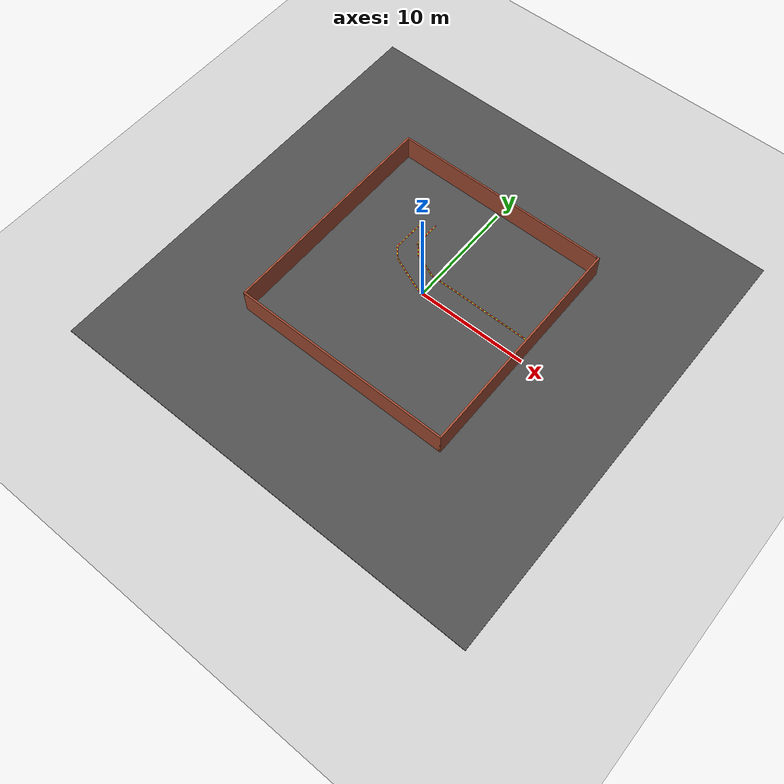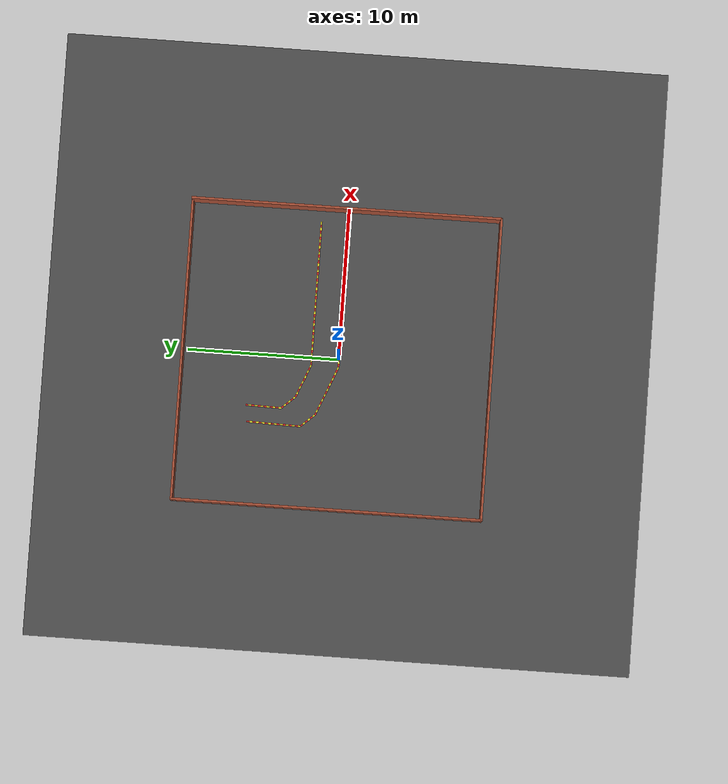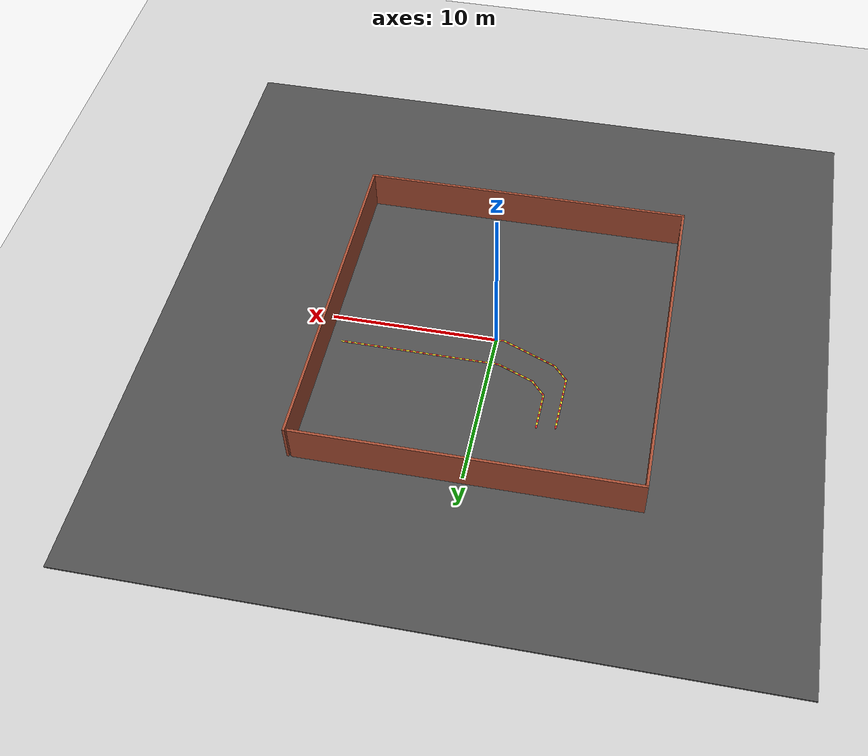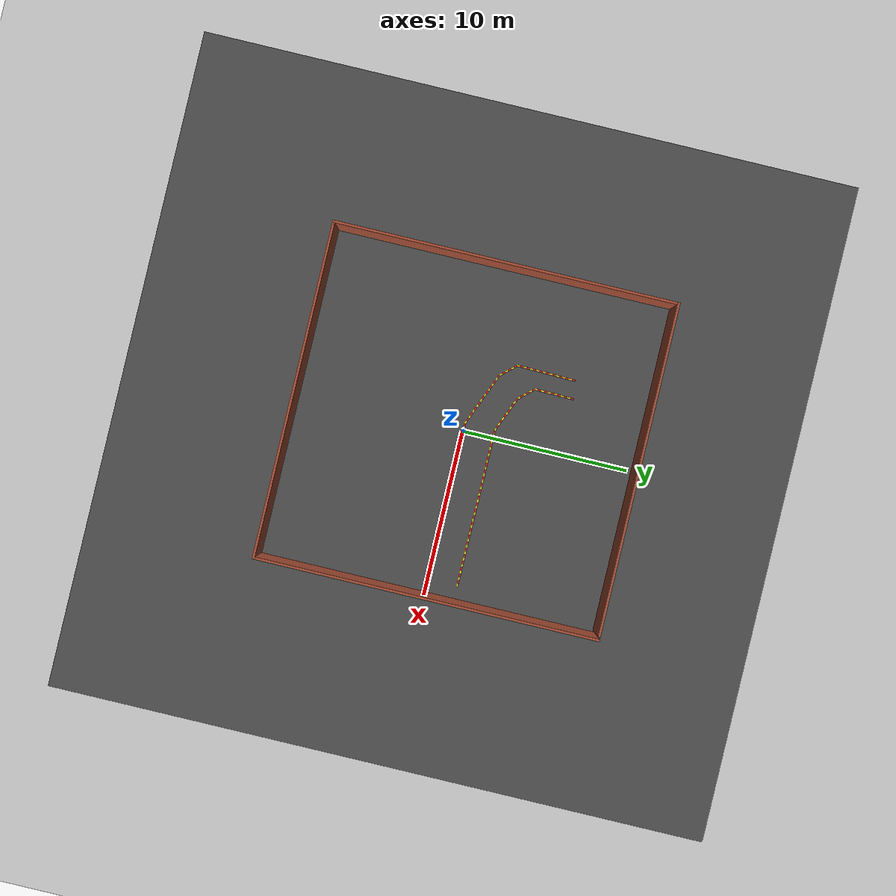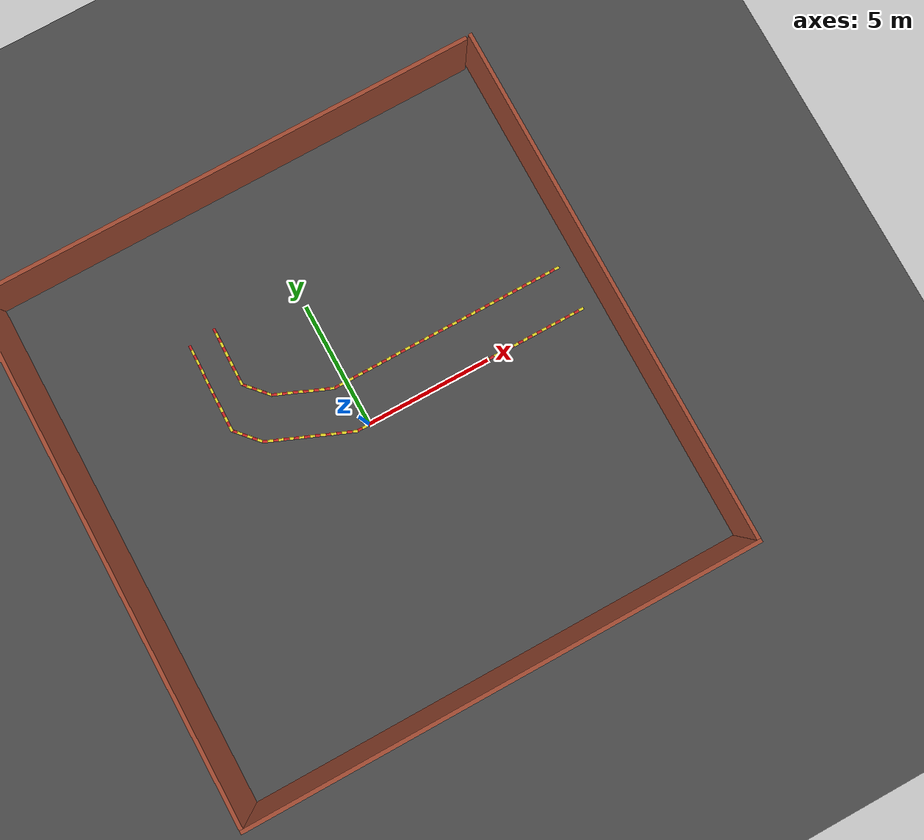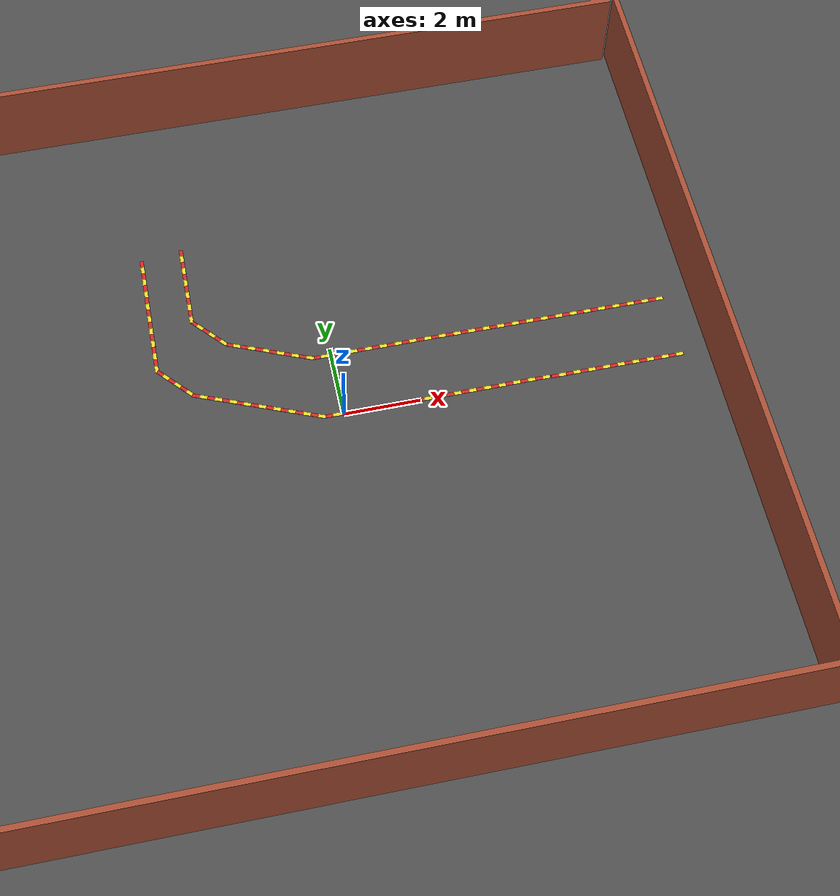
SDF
<sdf version="1.6">
 <world name="default">
  <light name="sun" type="directional">
   <pose>0 0 10 0 -0 0</pose>
   <diffuse>0.8 0.8 0.8 1</diffuse>
   <specular>0.2 0.2 0.2 1</specular>
   <attenuation>
    <range>1000</range>
    <constant>0.9</constant>
    <linear>0.01</linear>
    <quadratic>0.001</quadratic>
   </attenuation>
   <direction>-0.5 0.1 -0.9</direction>
  </light>
  <model name="camera_model">
   <pose>0 0 6.5 0 1.57079 0</pose>
   <static>1</static>
   <link name="camera_link">
    <sensor name="camera1" type="camera">
     <update_rate>60</update_rate>
     <visualize>1</visualize>
     <camera name="head">
      <horizontal_fov>1.39626</horizontal_fov>
      <image><width>640</width><height>480</height><format>R8G8B8</format></image>
      <clip><near>0.02</near><far>500</far></clip>
      <noise><type>gaussian</type><mean>0</mean><stddev>0.007</stddev></noise>
     </camera>
     <plugin name="camera_controller" filename="libgazebo_ros_camera.so">
      <ros>
       <namespace>demo_cam</namespace>
       <argument>image_raw:=image_demo</argument>
       <argument>camera_info:=camera_info_demo</argument>
      </ros>
     </plugin>
    </sensor>
   </link>
  </model>
  <light name="sun" type="directional">
   <pose>0 0 10 0 -0 0</pose>
   <diffuse>0.8 0.8 0.8 1</diffuse>
   <specular>0.2 0.2 0.2 1</specular>
   <attenuation>
    <range>1000</range>
    <constant>0.9</constant>
    <linear>0.01</linear>
    <quadratic>0.001</quadratic>
   </attenuation>
   <direction>-0.5 0.1 -0.9</direction>
  </light>
  <model name="ground_plane">
   <static>1</static>
   <link name="link">
    <collision name="collision">
     <geometry><plane><normal>0 0 1</normal><size>40 40</size></plane></geometry>
     <surface><friction><ode><mu>100</mu><mu2>50</mu2></ode></friction></surface>
    </collision>
    <visual name="visual">
     <cast_shadows>0</cast_shadows>
     <geometry><plane><normal>0 0 1</normal><size>40 40</size></plane></geometry>
     <material>
      <script><uri>file://media/materials/scripts/gazebo.material</uri><name>Gazebo/Grey</name></script>
     </material>
    </visual>
    <velocity_decay><linear>0</linear><angular>0</angular></velocity_decay>
   </link>
  </model>
  <physics name="default_physics" default="0" type="ode">
   <max_step_size>0.01</max_step_size>
   <real_time_factor>1</real_time_factor>
   <real_time_update_rate>100</real_time_update_rate>
  </physics>
  <scene><ambient>0.4 0.4 0.4 1</ambient><background>0.7 0.7 0.7 1</background><shadows>1</shadows></scene>
  <model name="asphalt_plane">
   <static>1</static>
   <link name="link">
    <collision name="collision"><geometry><box><size>40 40 0.1</size></box></geometry></collision>
    <visual name="visual">
     <cast_shadows>0</cast_shadows>
     <geometry><box><size>40 40 0.1</size></box></geometry>
     <material>
      <script>
       <uri>model://asphalt_plane/materials/scripts</uri>
       <uri>model://asphalt_plane/materials/textures</uri>
       <name>vrc/asphalt</name>
      </script>
     </material>
    </visual>
    <velocity_decay><linear>0</linear><angular>0</angular></velocity_decay>
   </link>
   <pose>0.433796 -0.497378 0 0 -0 0</pose>
  </model>
  <gravity>0 0 -9.8</gravity>
  <magnetic_field>6e-06 2.3e-05 -4.2e-05</magnetic_field>
  <atmosphere type="adiabatic"/>
  <audio><device>default</device></audio>
  <spherical_coordinates>
   <surface_model>EARTH_WGS84</surface_model>
   <latitude_deg>0</latitude_deg>
   <longitude_deg>0</longitude_deg>
   <elevation>0</elevation>
   <heading_deg>0</heading_deg>
  </spherical_coordinates>
  <model name="DashLine">
   <link name="link">
    <inertial>
     <mass>1</mass>
     <inertia>
      <ixx>0.166667</ixx>
      <ixy>0</ixy>
      <ixz>0</ixz>
      <iyy>0.166667</iyy>
      <iyz>0</iyz>
      <izz>0.166667</izz>
     </inertia>
    </inertial>
    <gravity>0</gravity>
    <visual name="ModelPreview_3::link::visual_3">
     <geometry><box><size>0.2 0.1 0.01</size></box></geometry>
     <material>
      <script><name>Gazebo/Yellow</name><uri>file://media/materials/scripts/gazebo.material</uri></script>
      <shader type="vertex"><normal_map>__default__</normal_map></shader>
      <ambient>0.988 0.914 0.31 1</ambient>
      <diffuse>0.7 0.7 0.7 1</diffuse>
      <specular>0.01 0.01 0.01 1</specular>
      <emissive>0 0 0 1</emissive>
     </material>
     <pose>0.2 0 0 0 -0 0</pose>
    </visual>
    <visual name="ModelPreview_6::link::visual_5">
     <geometry><box><size>0.2 0.1 0.01</size></box></geometry>
     <material>
      <script><name>Gazebo/Yellow</name><uri>file://media/materials/scripts/gazebo.material</uri></script>
      <shader type="vertex"><normal_map>__default__</normal_map></shader>
      <ambient>0.988 0.914 0.31 1</ambient>
      <diffuse>0.7 0.7 0.7 1</diffuse>
      <specular>0.01 0.01 0.01 1</specular>
      <emissive>0 0 0 1</emissive>
     </material>
     <pose>0.6 0 0 0 -0 0</pose>
    </visual>
    <visual name="ModelPreview_3::link::visual_4">
     <geometry><box><size>0.2 0.1 0.01</size></box></geometry>
     <material>
      <script><name>Gazebo/Red</name><uri>file://media/materials/scripts/gazebo.material</uri></script>
      <shader type="vertex"><normal_map>__default__</normal_map></shader>
      <ambient>0.937 0.161 0.161 1</ambient>
      <diffuse>0.7 0.7 0.7 1</diffuse>
      <specular>0.01 0.01 0.01 1</specular>
      <emissive>0 0 0 1</emissive>
     </material>
     <pose>0.4 0 0 0 -0 0</pose>
    </visual>
    <visual name="ModelPreview_3::link::visual_2">
     <geometry><box><size>0.2 0.1 0.01</size></box></geometry>
     <material>
      <script><name>Gazebo/Red</name><uri>file://media/materials/scripts/gazebo.material</uri></script>
      <shader type="vertex"><normal_map>__default__</normal_map></shader>
      <ambient>0.937 0.161 0.161 1</ambient>
      <diffuse>0.7 0.7 0.7 1</diffuse>
      <specular>0.01 0.01 0.01 1</specular>
      <emissive>0 0 0 1</emissive>
     </material>
    </visual>
    <visual name="visual">
     <geometry><box><size>0.2 0.1 0.01</size></box></geometry>
     <material>
      <script><name>Gazebo/Red</name><uri>file://media/materials/scripts/gazebo.material</uri></script>
      <shader type="vertex"><normal_map>__default__</normal_map></shader>
      <ambient>0.8 0 0 1</ambient>
      <diffuse>0.7 0.7 0.7 1</diffuse>
      <specular>0.01 0.01 0.01 1</specular>
      <emissive>0 0 0 1</emissive>
     </material>
     <pose>-0.4 0 0 0 -0 0</pose>
    </visual>
    <visual name="ModelPreview_3::link::visual_1">
     <geometry><box><size>0.2 0.1 0.01</size></box></geometry>
     <material>
      <script><name>Gazebo/Yellow</name><uri>file://media/materials/scripts/gazebo.material</uri></script>
      <shader type="vertex"><normal_map>__default__</normal_map></shader>
      <ambient>0.988 0.914 0.31 1</ambient>
      <diffuse>0.7 0.7 0.7 1</diffuse>
      <specular>0.01 0.01 0.01 1</specular>
      <emissive>0 0 0 1</emissive>
     </material>
     <pose>-0.2 0 0 0 -0 0</pose>
    </visual>
   </link>
   <static>0</static>
   <pose>0 0 0.05 0 -0 0</pose>
  </model>
  <model name="DashLine_clone">
   <link name="link">
    <inertial>
     <mass>1</mass>
     <inertia>
      <ixx>0.166667</ixx>
      <ixy>0</ixy>
      <ixz>0</ixz>
      <iyy>0.166667</iyy>
      <iyz>0</iyz>
      <izz>0.166667</izz>
     </inertia>
    </inertial>
    <gravity>0</gravity>
    <visual name="ModelPreview_3::link::visual_3">
     <geometry><box><size>0.2 0.1 0.01</size></box></geometry>
     <material>
      <script><name>Gazebo/Yellow</name><uri>file://media/materials/scripts/gazebo.material</uri></script>
      <shader type="vertex"><normal_map>__default__</normal_map></shader>
      <ambient>0.988 0.914 0.31 1</ambient>
      <diffuse>0.7 0.7 0.7 1</diffuse>
      <specular>0.01 0.01 0.01 1</specular>
      <emissive>0 0 0 1</emissive>
     </material>
     <pose>0.2 0 0 0 -0 0</pose>
    </visual>
    <visual name="ModelPreview_6::link::visual_5">
     <geometry><box><size>0.2 0.1 0.01</size></box></geometry>
     <material>
      <script><name>Gazebo/Yellow</name><uri>file://media/materials/scripts/gazebo.material</uri></script>
      <shader type="vertex"><normal_map>__default__</normal_map></shader>
      <ambient>0.988 0.914 0.31 1</ambient>
      <diffuse>0.7 0.7 0.7 1</diffuse>
      <specular>0.01 0.01 0.01 1</specular>
      <emissive>0 0 0 1</emissive>
     </material>
     <pose>0.6 0 0 0 -0 0</pose>
    </visual>
    <visual name="ModelPreview_3::link::visual_4">
     <geometry><box><size>0.2 0.1 0.01</size></box></geometry>
     <material>
      <script><name>Gazebo/Red</name><uri>file://media/materials/scripts/gazebo.material</uri></script>
      <shader type="vertex"><normal_map>__default__</normal_map></shader>
      <ambient>0.937 0.161 0.161 1</ambient>
      <diffuse>0.7 0.7 0.7 1</diffuse>
      <specular>0.01 0.01 0.01 1</specular>
      <emissive>0 0 0 1</emissive>
     </material>
     <pose>0.4 0 0 0 -0 0</pose>
    </visual>
    <visual name="ModelPreview_3::link::visual_2">
     <geometry><box><size>0.2 0.1 0.01</size></box></geometry>
     <material>
      <script><name>Gazebo/Red</name><uri>file://media/materials/scripts/gazebo.material</uri></script>
      <shader type="vertex"><normal_map>__default__</normal_map></shader>
      <ambient>0.937 0.161 0.161 1</ambient>
      <diffuse>0.7 0.7 0.7 1</diffuse>
      <specular>0.01 0.01 0.01 1</specular>
      <emissive>0 0 0 1</emissive>
     </material>
    </visual>
    <visual name="visual">
     <geometry><box><size>0.2 0.1 0.01</size></box></geometry>
     <material>
      <script><name>Gazebo/Red</name><uri>file://media/materials/scripts/gazebo.material</uri></script>
      <shader type="vertex"><normal_map>__default__</normal_map></shader>
      <ambient>0.8 0 0 1</ambient>
      <diffuse>0.7 0.7 0.7 1</diffuse>
      <specular>0.01 0.01 0.01 1</specular>
      <emissive>0 0 0 1</emissive>
     </material>
     <pose>-0.4 0 0 0 -0 0</pose>
    </visual>
    <visual name="ModelPreview_3::link::visual_1">
     <geometry><box><size>0.2 0.1 0.01</size></box></geometry>
     <material>
      <script><name>Gazebo/Yellow</name><uri>file://media/materials/scripts/gazebo.material</uri></script>
      <shader type="vertex"><normal_map>__default__</normal_map></shader>
      <ambient>0.988 0.914 0.31 1</ambient>
      <diffuse>0.7 0.7 0.7 1</diffuse>
      <specular>0.01 0.01 0.01 1</specular>
      <emissive>0 0 0 1</emissive>
     </material>
     <pose>-0.2 0 0 0 -0 0</pose>
    </visual>
   </link>
   <static>0</static>
   <pose>1.20456 0.000698 0.05 0 -0 0</pose>
  </model>
  <model name="DashLine_clone_clone">
   <link name="link">
    <inertial>
     <mass>1</mass>
     <inertia>
      <ixx>0.166667</ixx>
      <ixy>0</ixy>
      <ixz>0</ixz>
      <iyy>0.166667</iyy>
      <iyz>0</iyz>
      <izz>0.166667</izz>
     </inertia>
    </inertial>
    <gravity>0</gravity>
    <visual name="ModelPreview_3::link::visual_3">
     <geometry><box><size>0.2 0.1 0.01</size></box></geometry>
     <material>
      <script><name>Gazebo/Yellow</name><uri>file://media/materials/scripts/gazebo.material</uri></script>
      <shader type="vertex"><normal_map>__default__</normal_map></shader>
      <ambient>0.988 0.914 0.31 1</ambient>
      <diffuse>0.7 0.7 0.7 1</diffuse>
      <specular>0.01 0.01 0.01 1</specular>
      <emissive>0 0 0 1</emissive>
     </material>
     <pose>0.2 0 0 0 -0 0</pose>
    </visual>
    <visual name="ModelPreview_6::link::visual_5">
     <geometry><box><size>0.2 0.1 0.01</size></box></geometry>
     <material>
      <script><name>Gazebo/Yellow</name><uri>file://media/materials/scripts/gazebo.material</uri></script>
      <shader type="vertex"><normal_map>__default__</normal_map></shader>
      <ambient>0.988 0.914 0.31 1</ambient>
      <diffuse>0.7 0.7 0.7 1</diffuse>
      <specular>0.01 0.01 0.01 1</specular>
      <emissive>0 0 0 1</emissive>
     </material>
     <pose>0.6 0 0 0 -0 0</pose>
    </visual>
    <visual name="ModelPreview_3::link::visual_4">
     <geometry><box><size>0.2 0.1 0.01</size></box></geometry>
     <material>
      <script><name>Gazebo/Red</name><uri>file://media/materials/scripts/gazebo.material</uri></script>
      <shader type="vertex"><normal_map>__default__</normal_map></shader>
      <ambient>0.937 0.161 0.161 1</ambient>
      <diffuse>0.7 0.7 0.7 1</diffuse>
      <specular>0.01 0.01 0.01 1</specular>
      <emissive>0 0 0 1</emissive>
     </material>
     <pose>0.4 0 0 0 -0 0</pose>
    </visual>
    <visual name="ModelPreview_3::link::visual_2">
     <geometry><box><size>0.2 0.1 0.01</size></box></geometry>
     <material>
      <script><name>Gazebo/Red</name><uri>file://media/materials/scripts/gazebo.material</uri></script>
      <shader type="vertex"><normal_map>__default__</normal_map></shader>
      <ambient>0.937 0.161 0.161 1</ambient>
      <diffuse>0.7 0.7 0.7 1</diffuse>
      <specular>0.01 0.01 0.01 1</specular>
      <emissive>0 0 0 1</emissive>
     </material>
    </visual>
    <visual name="visual">
     <geometry><box><size>0.2 0.1 0.01</size></box></geometry>
     <material>
      <script><name>Gazebo/Red</name><uri>file://media/materials/scripts/gazebo.material</uri></script>
      <shader type="vertex"><normal_map>__default__</normal_map></shader>
      <ambient>0.8 0 0 1</ambient>
      <diffuse>0.7 0.7 0.7 1</diffuse>
      <specular>0.01 0.01 0.01 1</specular>
      <emissive>0 0 0 1</emissive>
     </material>
     <pose>-0.4 0 0 0 -0 0</pose>
    </visual>
    <visual name="ModelPreview_3::link::visual_1">
     <geometry><box><size>0.2 0.1 0.01</size></box></geometry>
     <material>
      <script><name>Gazebo/Yellow</name><uri>file://media/materials/scripts/gazebo.material</uri></script>
      <shader type="vertex"><normal_map>__default__</normal_map></shader>
      <ambient>0.988 0.914 0.31 1</ambient>
      <diffuse>0.7 0.7 0.7 1</diffuse>
      <specular>0.01 0.01 0.01 1</specular>
      <emissive>0 0 0 1</emissive>
     </material>
     <pose>-0.2 0 0 0 -0 0</pose>
    </visual>
   </link>
   <static>0</static>
   <pose>2.40797 -0.000483 0.05 0 -0 0</pose>
  </model>
  <model name="DashLine_clone_clone_clone">
   <link name="link">
    <inertial>
     <mass>1</mass>
     <inertia>
      <ixx>0.166667</ixx>
      <ixy>0</ixy>
      <ixz>0</ixz>
      <iyy>0.166667</iyy>
      <iyz>0</iyz>
      <izz>0.166667</izz>
     </inertia>
    </inertial>
    <gravity>0</gravity>
    <visual name="ModelPreview_3::link::visual_3">
     <geometry><box><size>0.2 0.1 0.01</size></box></geometry>
     <material>
      <script><name>Gazebo/Yellow</name><uri>file://media/materials/scripts/gazebo.material</uri></script>
      <shader type="vertex"><normal_map>__default__</normal_map></shader>
      <ambient>0.988 0.914 0.31 1</ambient>
      <diffuse>0.7 0.7 0.7 1</diffuse>
      <specular>0.01 0.01 0.01 1</specular>
      <emissive>0 0 0 1</emissive>
     </material>
     <pose>0.2 0 0 0 -0 0</pose>
    </visual>
    <visual name="ModelPreview_6::link::visual_5">
     <geometry><box><size>0.2 0.1 0.01</size></box></geometry>
     <material>
      <script><name>Gazebo/Yellow</name><uri>file://media/materials/scripts/gazebo.material</uri></script>
      <shader type="vertex"><normal_map>__default__</normal_map></shader>
      <ambient>0.988 0.914 0.31 1</ambient>
      <diffuse>0.7 0.7 0.7 1</diffuse>
      <specular>0.01 0.01 0.01 1</specular>
      <emissive>0 0 0 1</emissive>
     </material>
     <pose>0.6 0 0 0 -0 0</pose>
    </visual>
    <visual name="ModelPreview_3::link::visual_4">
     <geometry><box><size>0.2 0.1 0.01</size></box></geometry>
     <material>
      <script><name>Gazebo/Red</name><uri>file://media/materials/scripts/gazebo.material</uri></script>
      <shader type="vertex"><normal_map>__default__</normal_map></shader>
      <ambient>0.937 0.161 0.161 1</ambient>
      <diffuse>0.7 0.7 0.7 1</diffuse>
      <specular>0.01 0.01 0.01 1</specular>
      <emissive>0 0 0 1</emissive>
     </material>
     <pose>0.4 0 0 0 -0 0</pose>
    </visual>
    <visual name="ModelPreview_3::link::visual_2">
     <geometry><box><size>0.2 0.1 0.01</size></box></geometry>
     <material>
      <script><name>Gazebo/Red</name><uri>file://media/materials/scripts/gazebo.material</uri></script>
      <shader type="vertex"><normal_map>__default__</normal_map></shader>
      <ambient>0.937 0.161 0.161 1</ambient>
      <diffuse>0.7 0.7 0.7 1</diffuse>
      <specular>0.01 0.01 0.01 1</specular>
      <emissive>0 0 0 1</emissive>
     </material>
    </visual>
    <visual name="visual">
     <geometry><box><size>0.2 0.1 0.01</size></box></geometry>
     <material>
      <script><name>Gazebo/Red</name><uri>file://media/materials/scripts/gazebo.material</uri></script>
      <shader type="vertex"><normal_map>__default__</normal_map></shader>
      <ambient>0.8 0 0 1</ambient>
      <diffuse>0.7 0.7 0.7 1</diffuse>
      <specular>0.01 0.01 0.01 1</specular>
      <emissive>0 0 0 1</emissive>
     </material>
     <pose>-0.4 0 0 0 -0 0</pose>
    </visual>
    <visual name="ModelPreview_3::link::visual_1">
     <geometry><box><size>0.2 0.1 0.01</size></box></geometry>
     <material>
      <script><name>Gazebo/Yellow</name><uri>file://media/materials/scripts/gazebo.material</uri></script>
      <shader type="vertex"><normal_map>__default__</normal_map></shader>
      <ambient>0.988 0.914 0.31 1</ambient>
      <diffuse>0.7 0.7 0.7 1</diffuse>
      <specular>0.01 0.01 0.01 1</specular>
      <emissive>0 0 0 1</emissive>
     </material>
     <pose>-0.2 0 0 0 -0 0</pose>
    </visual>
   </link>
   <static>0</static>
   <pose>3.60612 0.00353 0.05 0 -0 0</pose>
  </model>
  <model name="DashLine_clone_clone_clone_0">
   <link name="link">
    <inertial>
     <mass>1</mass>
     <inertia>
      <ixx>0.166667</ixx>
      <ixy>0</ixy>
      <ixz>0</ixz>
      <iyy>0.166667</iyy>
      <iyz>0</iyz>
      <izz>0.166667</izz>
     </inertia>
    </inertial>
    <gravity>0</gravity>
    <visual name="ModelPreview_3::link::visual_3">
     <geometry><box><size>0.2 0.1 0.01</size></box></geometry>
     <material>
      <script><name>Gazebo/Yellow</name><uri>file://media/materials/scripts/gazebo.material</uri></script>
      <shader type="vertex"><normal_map>__default__</normal_map></shader>
      <ambient>0.988 0.914 0.31 1</ambient>
      <diffuse>0.7 0.7 0.7 1</diffuse>
      <specular>0.01 0.01 0.01 1</specular>
      <emissive>0 0 0 1</emissive>
     </material>
     <pose>0.2 0 0 0 -0 0</pose>
    </visual>
    <visual name="ModelPreview_6::link::visual_5">
     <geometry><box><size>0.2 0.1 0.01</size></box></geometry>
     <material>
      <script><name>Gazebo/Yellow</name><uri>file://media/materials/scripts/gazebo.material</uri></script>
      <shader type="vertex"><normal_map>__default__</normal_map></shader>
      <ambient>0.988 0.914 0.31 1</ambient>
      <diffuse>0.7 0.7 0.7 1</diffuse>
      <specular>0.01 0.01 0.01 1</specular>
      <emissive>0 0 0 1</emissive>
     </material>
     <pose>0.6 0 0 0 -0 0</pose>
    </visual>
    <visual name="ModelPreview_3::link::visual_4">
     <geometry><box><size>0.2 0.1 0.01</size></box></geometry>
     <material>
      <script><name>Gazebo/Red</name><uri>file://media/materials/scripts/gazebo.material</uri></script>
      <shader type="vertex"><normal_map>__default__</normal_map></shader>
      <ambient>0.937 0.161 0.161 1</ambient>
      <diffuse>0.7 0.7 0.7 1</diffuse>
      <specular>0.01 0.01 0.01 1</specular>
      <emissive>0 0 0 1</emissive>
     </material>
     <pose>0.4 0 0 0 -0 0</pose>
    </visual>
    <visual name="ModelPreview_3::link::visual_2">
     <geometry><box><size>0.2 0.1 0.01</size></box></geometry>
     <material>
      <script><name>Gazebo/Red</name><uri>file://media/materials/scripts/gazebo.material</uri></script>
      <shader type="vertex"><normal_map>__default__</normal_map></shader>
      <ambient>0.937 0.161 0.161 1</ambient>
      <diffuse>0.7 0.7 0.7 1</diffuse>
      <specular>0.01 0.01 0.01 1</specular>
      <emissive>0 0 0 1</emissive>
     </material>
    </visual>
    <visual name="visual">
     <geometry><box><size>0.2 0.1 0.01</size></box></geometry>
     <material>
      <script><name>Gazebo/Red</name><uri>file://media/materials/scripts/gazebo.material</uri></script>
      <shader type="vertex"><normal_map>__default__</normal_map></shader>
      <ambient>0.8 0 0 1</ambient>
      <diffuse>0.7 0.7 0.7 1</diffuse>
      <specular>0.01 0.01 0.01 1</specular>
      <emissive>0 0 0 1</emissive>
     </material>
     <pose>-0.4 0 0 0 -0 0</pose>
    </visual>
    <visual name="ModelPreview_3::link::visual_1">
     <geometry><box><size>0.2 0.1 0.01</size></box></geometry>
     <material>
      <script><name>Gazebo/Yellow</name><uri>file://media/materials/scripts/gazebo.material</uri></script>
      <shader type="vertex"><normal_map>__default__</normal_map></shader>
      <ambient>0.988 0.914 0.31 1</ambient>
      <diffuse>0.7 0.7 0.7 1</diffuse>
      <specular>0.01 0.01 0.01 1</specular>
      <emissive>0 0 0 1</emissive>
     </material>
     <pose>-0.2 0 0 0 -0 0</pose>
    </visual>
   </link>
   <static>0</static>
   <pose>4.79034 0.009955 0.05 0 -0 0</pose>
  </model>
  <model name="DashLine_clone_clone_clone_1">
   <link name="link">
    <inertial>
     <mass>1</mass>
     <inertia>
      <ixx>0.166667</ixx>
      <ixy>0</ixy>
      <ixz>0</ixz>
      <iyy>0.166667</iyy>
      <iyz>0</iyz>
      <izz>0.166667</izz>
     </inertia>
    </inertial>
    <gravity>0</gravity>
    <visual name="ModelPreview_3::link::visual_3">
     <geometry><box><size>0.2 0.1 0.01</size></box></geometry>
     <material>
      <script><name>Gazebo/Yellow</name><uri>file://media/materials/scripts/gazebo.material</uri></script>
      <shader type="vertex"><normal_map>__default__</normal_map></shader>
      <ambient>0.988 0.914 0.31 1</ambient>
      <diffuse>0.7 0.7 0.7 1</diffuse>
      <specular>0.01 0.01 0.01 1</specular>
      <emissive>0 0 0 1</emissive>
     </material>
     <pose>0.2 0 0 0 -0 0</pose>
    </visual>
    <visual name="ModelPreview_6::link::visual_5">
     <geometry><box><size>0.2 0.1 0.01</size></box></geometry>
     <material>
      <script><name>Gazebo/Yellow</name><uri>file://media/materials/scripts/gazebo.material</uri></script>
      <shader type="vertex"><normal_map>__default__</normal_map></shader>
      <ambient>0.988 0.914 0.31 1</ambient>
      <diffuse>0.7 0.7 0.7 1</diffuse>
      <specular>0.01 0.01 0.01 1</specular>
      <emissive>0 0 0 1</emissive>
     </material>
     <pose>0.6 0 0 0 -0 0</pose>
    </visual>
    <visual name="ModelPreview_3::link::visual_4">
     <geometry><box><size>0.2 0.1 0.01</size></box></geometry>
     <material>
      <script><name>Gazebo/Red</name><uri>file://media/materials/scripts/gazebo.material</uri></script>
      <shader type="vertex"><normal_map>__default__</normal_map></shader>
      <ambient>0.937 0.161 0.161 1</ambient>
      <diffuse>0.7 0.7 0.7 1</diffuse>
      <specular>0.01 0.01 0.01 1</specular>
      <emissive>0 0 0 1</emissive>
     </material>
     <pose>0.4 0 0 0 -0 0</pose>
    </visual>
    <visual name="ModelPreview_3::link::visual_2">
     <geometry><box><size>0.2 0.1 0.01</size></box></geometry>
     <material>
      <script><name>Gazebo/Red</name><uri>file://media/materials/scripts/gazebo.material</uri></script>
      <shader type="vertex"><normal_map>__default__</normal_map></shader>
      <ambient>0.937 0.161 0.161 1</ambient>
      <diffuse>0.7 0.7 0.7 1</diffuse>
      <specular>0.01 0.01 0.01 1</specular>
      <emissive>0 0 0 1</emissive>
     </material>
    </visual>
    <visual name="visual">
     <geometry><box><size>0.2 0.1 0.01</size></box></geometry>
     <material>
      <script><name>Gazebo/Red</name><uri>file://media/materials/scripts/gazebo.material</uri></script>
      <shader type="vertex"><normal_map>__default__</normal_map></shader>
      <ambient>0.8 0 0 1</ambient>
      <diffuse>0.7 0.7 0.7 1</diffuse>
      <specular>0.01 0.01 0.01 1</specular>
      <emissive>0 0 0 1</emissive>
     </material>
     <pose>-0.4 0 0 0 -0 0</pose>
    </visual>
    <visual name="ModelPreview_3::link::visual_1">
     <geometry><box><size>0.2 0.1 0.01</size></box></geometry>
     <material>
      <script><name>Gazebo/Yellow</name><uri>file://media/materials/scripts/gazebo.material</uri></script>
      <shader type="vertex"><normal_map>__default__</normal_map></shader>
      <ambient>0.988 0.914 0.31 1</ambient>
      <diffuse>0.7 0.7 0.7 1</diffuse>
      <specular>0.01 0.01 0.01 1</specular>
      <emissive>0 0 0 1</emissive>
     </material>
     <pose>-0.2 0 0 0 -0 0</pose>
    </visual>
   </link>
   <static>0</static>
   <pose>6.01721 -0.001869 0.05 0 -0 0</pose>
  </model>
  <model name="DashLine_clone_clone_clone_2">
   <link name="link">
    <inertial>
     <mass>1</mass>
     <inertia>
      <ixx>0.166667</ixx>
      <ixy>0</ixy>
      <ixz>0</ixz>
      <iyy>0.166667</iyy>
      <iyz>0</iyz>
      <izz>0.166667</izz>
     </inertia>
    </inertial>
    <gravity>0</gravity>
    <visual name="ModelPreview_3::link::visual_3">
     <geometry><box><size>0.2 0.1 0.01</size></box></geometry>
     <material>
      <script><name>Gazebo/Yellow</name><uri>file://media/materials/scripts/gazebo.material</uri></script>
      <shader type="vertex"><normal_map>__default__</normal_map></shader>
      <ambient>0.988 0.914 0.31 1</ambient>
      <diffuse>0.7 0.7 0.7 1</diffuse>
      <specular>0.01 0.01 0.01 1</specular>
      <emissive>0 0 0 1</emissive>
     </material>
     <pose>0.2 0 0 0 -0 0</pose>
    </visual>
    <visual name="ModelPreview_6::link::visual_5">
     <geometry><box><size>0.2 0.1 0.01</size></box></geometry>
     <material>
      <script><name>Gazebo/Yellow</name><uri>file://media/materials/scripts/gazebo.material</uri></script>
      <shader type="vertex"><normal_map>__default__</normal_map></shader>
      <ambient>0.988 0.914 0.31 1</ambient>
      <diffuse>0.7 0.7 0.7 1</diffuse>
      <specular>0.01 0.01 0.01 1</specular>
      <emissive>0 0 0 1</emissive>
     </material>
     <pose>0.6 0 0 0 -0 0</pose>
    </visual>
    <visual name="ModelPreview_3::link::visual_4">
     <geometry><box><size>0.2 0.1 0.01</size></box></geometry>
     <material>
      <script><name>Gazebo/Red</name><uri>file://media/materials/scripts/gazebo.material</uri></script>
      <shader type="vertex"><normal_map>__default__</normal_map></shader>
      <ambient>0.937 0.161 0.161 1</ambient>
      <diffuse>0.7 0.7 0.7 1</diffuse>
      <specular>0.01 0.01 0.01 1</specular>
      <emissive>0 0 0 1</emissive>
     </material>
     <pose>0.4 0 0 0 -0 0</pose>
    </visual>
    <visual name="ModelPreview_3::link::visual_2">
     <geometry><box><size>0.2 0.1 0.01</size></box></geometry>
     <material>
      <script><name>Gazebo/Red</name><uri>file://media/materials/scripts/gazebo.material</uri></script>
      <shader type="vertex"><normal_map>__default__</normal_map></shader>
      <ambient>0.937 0.161 0.161 1</ambient>
      <diffuse>0.7 0.7 0.7 1</diffuse>
      <specular>0.01 0.01 0.01 1</specular>
      <emissive>0 0 0 1</emissive>
     </material>
    </visual>
    <visual name="visual">
     <geometry><box><size>0.2 0.1 0.01</size></box></geometry>
     <material>
      <script><name>Gazebo/Red</name><uri>file://media/materials/scripts/gazebo.material</uri></script>
      <shader type="vertex"><normal_map>__default__</normal_map></shader>
      <ambient>0.8 0 0 1</ambient>
      <diffuse>0.7 0.7 0.7 1</diffuse>
      <specular>0.01 0.01 0.01 1</specular>
      <emissive>0 0 0 1</emissive>
     </material>
     <pose>-0.4 0 0 0 -0 0</pose>
    </visual>
    <visual name="ModelPreview_3::link::visual_1">
     <geometry><box><size>0.2 0.1 0.01</size></box></geometry>
     <material>
      <script><name>Gazebo/Yellow</name><uri>file://media/materials/scripts/gazebo.material</uri></script>
      <shader type="vertex"><normal_map>__default__</normal_map></shader>
      <ambient>0.988 0.914 0.31 1</ambient>
      <diffuse>0.7 0.7 0.7 1</diffuse>
      <specular>0.01 0.01 0.01 1</specular>
      <emissive>0 0 0 1</emissive>
     </material>
     <pose>-0.2 0 0 0 -0 0</pose>
    </visual>
   </link>
   <static>0</static>
   <pose>7.21478 -0.00075 0.05 0 -0 0</pose>
  </model>
  <model name="DashLine_clone_clone_clone_3">
   <link name="link">
    <inertial>
     <mass>1</mass>
     <inertia>
      <ixx>0.166667</ixx>
      <ixy>0</ixy>
      <ixz>0</ixz>
      <iyy>0.166667</iyy>
      <iyz>0</iyz>
      <izz>0.166667</izz>
     </inertia>
    </inertial>
    <gravity>0</gravity>
    <visual name="ModelPreview_3::link::visual_3">
     <geometry><box><size>0.2 0.1 0.01</size></box></geometry>
     <material>
      <script><name>Gazebo/Yellow</name><uri>file://media/materials/scripts/gazebo.material</uri></script>
      <shader type="vertex"><normal_map>__default__</normal_map></shader>
      <ambient>0.988 0.914 0.31 1</ambient>
      <diffuse>0.7 0.7 0.7 1</diffuse>
      <specular>0.01 0.01 0.01 1</specular>
      <emissive>0 0 0 1</emissive>
     </material>
     <pose>0.2 0 0 0 -0 0</pose>
    </visual>
    <visual name="ModelPreview_6::link::visual_5">
     <geometry><box><size>0.2 0.1 0.01</size></box></geometry>
     <material>
      <script><name>Gazebo/Yellow</name><uri>file://media/materials/scripts/gazebo.material</uri></script>
      <shader type="vertex"><normal_map>__default__</normal_map></shader>
      <ambient>0.988 0.914 0.31 1</ambient>
      <diffuse>0.7 0.7 0.7 1</diffuse>
      <specular>0.01 0.01 0.01 1</specular>
      <emissive>0 0 0 1</emissive>
     </material>
     <pose>0.6 0 0 0 -0 0</pose>
    </visual>
    <visual name="ModelPreview_3::link::visual_4">
     <geometry><box><size>0.2 0.1 0.01</size></box></geometry>
     <material>
      <script><name>Gazebo/Red</name><uri>file://media/materials/scripts/gazebo.material</uri></script>
      <shader type="vertex"><normal_map>__default__</normal_map></shader>
      <ambient>0.937 0.161 0.161 1</ambient>
      <diffuse>0.7 0.7 0.7 1</diffuse>
      <specular>0.01 0.01 0.01 1</specular>
      <emissive>0 0 0 1</emissive>
     </material>
     <pose>0.4 0 0 0 -0 0</pose>
    </visual>
    <visual name="ModelPreview_3::link::visual_2">
     <geometry><box><size>0.2 0.1 0.01</size></box></geometry>
     <material>
      <script><name>Gazebo/Red</name><uri>file://media/materials/scripts/gazebo.material</uri></script>
      <shader type="vertex"><normal_map>__default__</normal_map></shader>
      <ambient>0.937 0.161 0.161 1</ambient>
      <diffuse>0.7 0.7 0.7 1</diffuse>
      <specular>0.01 0.01 0.01 1</specular>
      <emissive>0 0 0 1</emissive>
     </material>
    </visual>
    <visual name="visual">
     <geometry><box><size>0.2 0.1 0.01</size></box></geometry>
     <material>
      <script><name>Gazebo/Red</name><uri>file://media/materials/scripts/gazebo.material</uri></script>
      <shader type="vertex"><normal_map>__default__</normal_map></shader>
      <ambient>0.8 0 0 1</ambient>
      <diffuse>0.7 0.7 0.7 1</diffuse>
      <specular>0.01 0.01 0.01 1</specular>
      <emissive>0 0 0 1</emissive>
     </material>
     <pose>-0.4 0 0 0 -0 0</pose>
    </visual>
    <visual name="ModelPreview_3::link::visual_1">
     <geometry><box><size>0.2 0.1 0.01</size></box></geometry>
     <material>
      <script><name>Gazebo/Yellow</name><uri>file://media/materials/scripts/gazebo.material</uri></script>
      <shader type="vertex"><normal_map>__default__</normal_map></shader>
      <ambient>0.988 0.914 0.31 1</ambient>
      <diffuse>0.7 0.7 0.7 1</diffuse>
      <specular>0.01 0.01 0.01 1</specular>
      <emissive>0 0 0 1</emissive>
     </material>
     <pose>-0.2 0 0 0 -0 0</pose>
    </visual>
   </link>
   <static>0</static>
   <pose>8.40762 -0.005132 0.05 0 -0 0</pose>
  </model>
  <model name="DashLine_clone_clone_clone_4">
   <link name="link">
    <inertial>
     <mass>1</mass>
     <inertia>
      <ixx>0.166667</ixx>
      <ixy>0</ixy>
      <ixz>0</ixz>
      <iyy>0.166667</iyy>
      <iyz>0</iyz>
      <izz>0.166667</izz>
     </inertia>
    </inertial>
    <gravity>0</gravity>
    <visual name="ModelPreview_3::link::visual_3">
     <geometry><box><size>0.2 0.1 0.01</size></box></geometry>
     <material>
      <script><name>Gazebo/Yellow</name><uri>file://media/materials/scripts/gazebo.material</uri></script>
      <shader type="vertex"><normal_map>__default__</normal_map></shader>
      <ambient>0.988 0.914 0.31 1</ambient>
      <diffuse>0.7 0.7 0.7 1</diffuse>
      <specular>0.01 0.01 0.01 1</specular>
      <emissive>0 0 0 1</emissive>
     </material>
     <pose>0.2 0 0 0 -0 0</pose>
    </visual>
    <visual name="ModelPreview_6::link::visual_5">
     <geometry><box><size>0.2 0.1 0.01</size></box></geometry>
     <material>
      <script><name>Gazebo/Yellow</name><uri>file://media/materials/scripts/gazebo.material</uri></script>
      <shader type="vertex"><normal_map>__default__</normal_map></shader>
      <ambient>0.988 0.914 0.31 1</ambient>
      <diffuse>0.7 0.7 0.7 1</diffuse>
      <specular>0.01 0.01 0.01 1</specular>
      <emissive>0 0 0 1</emissive>
     </material>
     <pose>0.6 0 0 0 -0 0</pose>
    </visual>
    <visual name="ModelPreview_3::link::visual_4">
     <geometry><box><size>0.2 0.1 0.01</size></box></geometry>
     <material>
      <script><name>Gazebo/Red</name><uri>file://media/materials/scripts/gazebo.material</uri></script>
      <shader type="vertex"><normal_map>__default__</normal_map></shader>
      <ambient>0.937 0.161 0.161 1</ambient>
      <diffuse>0.7 0.7 0.7 1</diffuse>
      <specular>0.01 0.01 0.01 1</specular>
      <emissive>0 0 0 1</emissive>
     </material>
     <pose>0.4 0 0 0 -0 0</pose>
    </visual>
    <visual name="ModelPreview_3::link::visual_2">
     <geometry><box><size>0.2 0.1 0.01</size></box></geometry>
     <material>
      <script><name>Gazebo/Red</name><uri>file://media/materials/scripts/gazebo.material</uri></script>
      <shader type="vertex"><normal_map>__default__</normal_map></shader>
      <ambient>0.937 0.161 0.161 1</ambient>
      <diffuse>0.7 0.7 0.7 1</diffuse>
      <specular>0.01 0.01 0.01 1</specular>
      <emissive>0 0 0 1</emissive>
     </material>
    </visual>
    <visual name="visual">
     <geometry><box><size>0.2 0.1 0.01</size></box></geometry>
     <material>
      <script><name>Gazebo/Red</name><uri>file://media/materials/scripts/gazebo.material</uri></script>
      <shader type="vertex"><normal_map>__default__</normal_map></shader>
      <ambient>0.8 0 0 1</ambient>
      <diffuse>0.7 0.7 0.7 1</diffuse>
      <specular>0.01 0.01 0.01 1</specular>
      <emissive>0 0 0 1</emissive>
     </material>
     <pose>-0.4 0 0 0 -0 0</pose>
    </visual>
    <visual name="ModelPreview_3::link::visual_1">
     <geometry><box><size>0.2 0.1 0.01</size></box></geometry>
     <material>
      <script><name>Gazebo/Yellow</name><uri>file://media/materials/scripts/gazebo.material</uri></script>
      <shader type="vertex"><normal_map>__default__</normal_map></shader>
      <ambient>0.988 0.914 0.31 1</ambient>
      <diffuse>0.7 0.7 0.7 1</diffuse>
      <specular>0.01 0.01 0.01 1</specular>
      <emissive>0 0 0 1</emissive>
     </material>
     <pose>-0.2 0 0 0 -0 0</pose>
    </visual>
   </link>
   <static>0</static>
   <pose>8.36917 1.7952 0.05 0 -0 0</pose>
  </model>
  <model name="DashLine_clone_clone_clone_5">
   <link name="link">
    <inertial>
     <mass>1</mass>
     <inertia>
      <ixx>0.166667</ixx>
      <ixy>0</ixy>
      <ixz>0</ixz>
      <iyy>0.166667</iyy>
      <iyz>0</iyz>
      <izz>0.166667</izz>
     </inertia>
    </inertial>
    <gravity>0</gravity>
    <visual name="ModelPreview_3::link::visual_3">
     <geometry><box><size>0.2 0.1 0.01</size></box></geometry>
     <material>
      <script><name>Gazebo/Yellow</name><uri>file://media/materials/scripts/gazebo.material</uri></script>
      <shader type="vertex"><normal_map>__default__</normal_map></shader>
      <ambient>0.988 0.914 0.31 1</ambient>
      <diffuse>0.7 0.7 0.7 1</diffuse>
      <specular>0.01 0.01 0.01 1</specular>
      <emissive>0 0 0 1</emissive>
     </material>
     <pose>0.2 0 0 0 -0 0</pose>
    </visual>
    <visual name="ModelPreview_6::link::visual_5">
     <geometry><box><size>0.2 0.1 0.01</size></box></geometry>
     <material>
      <script><name>Gazebo/Yellow</name><uri>file://media/materials/scripts/gazebo.material</uri></script>
      <shader type="vertex"><normal_map>__default__</normal_map></shader>
      <ambient>0.988 0.914 0.31 1</ambient>
      <diffuse>0.7 0.7 0.7 1</diffuse>
      <specular>0.01 0.01 0.01 1</specular>
      <emissive>0 0 0 1</emissive>
     </material>
     <pose>0.6 0 0 0 -0 0</pose>
    </visual>
    <visual name="ModelPreview_3::link::visual_4">
     <geometry><box><size>0.2 0.1 0.01</size></box></geometry>
     <material>
      <script><name>Gazebo/Red</name><uri>file://media/materials/scripts/gazebo.material</uri></script>
      <shader type="vertex"><normal_map>__default__</normal_map></shader>
      <ambient>0.937 0.161 0.161 1</ambient>
      <diffuse>0.7 0.7 0.7 1</diffuse>
      <specular>0.01 0.01 0.01 1</specular>
      <emissive>0 0 0 1</emissive>
     </material>
     <pose>0.4 0 0 0 -0 0</pose>
    </visual>
    <visual name="ModelPreview_3::link::visual_2">
     <geometry><box><size>0.2 0.1 0.01</size></box></geometry>
     <material>
      <script><name>Gazebo/Red</name><uri>file://media/materials/scripts/gazebo.material</uri></script>
      <shader type="vertex"><normal_map>__default__</normal_map></shader>
      <ambient>0.937 0.161 0.161 1</ambient>
      <diffuse>0.7 0.7 0.7 1</diffuse>
      <specular>0.01 0.01 0.01 1</specular>
      <emissive>0 0 0 1</emissive>
     </material>
    </visual>
    <visual name="visual">
     <geometry><box><size>0.2 0.1 0.01</size></box></geometry>
     <material>
      <script><name>Gazebo/Red</name><uri>file://media/materials/scripts/gazebo.material</uri></script>
      <shader type="vertex"><normal_map>__default__</normal_map></shader>
      <ambient>0.8 0 0 1</ambient>
      <diffuse>0.7 0.7 0.7 1</diffuse>
      <specular>0.01 0.01 0.01 1</specular>
      <emissive>0 0 0 1</emissive>
     </material>
     <pose>-0.4 0 0 0 -0 0</pose>
    </visual>
    <visual name="ModelPreview_3::link::visual_1">
     <geometry><box><size>0.2 0.1 0.01</size></box></geometry>
     <material>
      <script><name>Gazebo/Yellow</name><uri>file://media/materials/scripts/gazebo.material</uri></script>
      <shader type="vertex"><normal_map>__default__</normal_map></shader>
      <ambient>0.988 0.914 0.31 1</ambient>
      <diffuse>0.7 0.7 0.7 1</diffuse>
      <specular>0.01 0.01 0.01 1</specular>
      <emissive>0 0 0 1</emissive>
     </material>
     <pose>-0.2 0 0 0 -0 0</pose>
    </visual>
   </link>
   <static>0</static>
   <pose>7.16738 1.79779 0.05 0 -0 0</pose>
  </model>
  <model name="DashLine_clone_clone_clone_6">
   <link name="link">
    <inertial>
     <mass>1</mass>
     <inertia>
      <ixx>0.166667</ixx>
      <ixy>0</ixy>
      <ixz>0</ixz>
      <iyy>0.166667</iyy>
      <iyz>0</iyz>
      <izz>0.166667</izz>
     </inertia>
    </inertial>
    <gravity>0</gravity>
    <visual name="ModelPreview_3::link::visual_3">
     <geometry><box><size>0.2 0.1 0.01</size></box></geometry>
     <material>
      <script><name>Gazebo/Yellow</name><uri>file://media/materials/scripts/gazebo.material</uri></script>
      <shader type="vertex"><normal_map>__default__</normal_map></shader>
      <ambient>0.988 0.914 0.31 1</ambient>
      <diffuse>0.7 0.7 0.7 1</diffuse>
      <specular>0.01 0.01 0.01 1</specular>
      <emissive>0 0 0 1</emissive>
     </material>
     <pose>0.2 0 0 0 -0 0</pose>
    </visual>
    <visual name="ModelPreview_6::link::visual_5">
     <geometry><box><size>0.2 0.1 0.01</size></box></geometry>
     <material>
      <script><name>Gazebo/Yellow</name><uri>file://media/materials/scripts/gazebo.material</uri></script>
      <shader type="vertex"><normal_map>__default__</normal_map></shader>
      <ambient>0.988 0.914 0.31 1</ambient>
      <diffuse>0.7 0.7 0.7 1</diffuse>
      <specular>0.01 0.01 0.01 1</specular>
      <emissive>0 0 0 1</emissive>
     </material>
     <pose>0.6 0 0 0 -0 0</pose>
    </visual>
    <visual name="ModelPreview_3::link::visual_4">
     <geometry><box><size>0.2 0.1 0.01</size></box></geometry>
     <material>
      <script><name>Gazebo/Red</name><uri>file://media/materials/scripts/gazebo.material</uri></script>
      <shader type="vertex"><normal_map>__default__</normal_map></shader>
      <ambient>0.937 0.161 0.161 1</ambient>
      <diffuse>0.7 0.7 0.7 1</diffuse>
      <specular>0.01 0.01 0.01 1</specular>
      <emissive>0 0 0 1</emissive>
     </material>
     <pose>0.4 0 0 0 -0 0</pose>
    </visual>
    <visual name="ModelPreview_3::link::visual_2">
     <geometry><box><size>0.2 0.1 0.01</size></box></geometry>
     <material>
      <script><name>Gazebo/Red</name><uri>file://media/materials/scripts/gazebo.material</uri></script>
      <shader type="vertex"><normal_map>__default__</normal_map></shader>
      <ambient>0.937 0.161 0.161 1</ambient>
      <diffuse>0.7 0.7 0.7 1</diffuse>
      <specular>0.01 0.01 0.01 1</specular>
      <emissive>0 0 0 1</emissive>
     </material>
    </visual>
    <visual name="visual">
     <geometry><box><size>0.2 0.1 0.01</size></box></geometry>
     <material>
      <script><name>Gazebo/Red</name><uri>file://media/materials/scripts/gazebo.material</uri></script>
      <shader type="vertex"><normal_map>__default__</normal_map></shader>
      <ambient>0.8 0 0 1</ambient>
      <diffuse>0.7 0.7 0.7 1</diffuse>
      <specular>0.01 0.01 0.01 1</specular>
      <emissive>0 0 0 1</emissive>
     </material>
     <pose>-0.4 0 0 0 -0 0</pose>
    </visual>
    <visual name="ModelPreview_3::link::visual_1">
     <geometry><box><size>0.2 0.1 0.01</size></box></geometry>
     <material>
      <script><name>Gazebo/Yellow</name><uri>file://media/materials/scripts/gazebo.material</uri></script>
      <shader type="vertex"><normal_map>__default__</normal_map></shader>
      <ambient>0.988 0.914 0.31 1</ambient>
      <diffuse>0.7 0.7 0.7 1</diffuse>
      <specular>0.01 0.01 0.01 1</specular>
      <emissive>0 0 0 1</emissive>
     </material>
     <pose>-0.2 0 0 0 -0 0</pose>
    </visual>
   </link>
   <static>0</static>
   <pose>5.9877 1.80097 0.05 0 -0 0</pose>
  </model>
  <model name="DashLine_clone_clone_clone_7">
   <link name="link">
    <inertial>
     <mass>1</mass>
     <inertia>
      <ixx>0.166667</ixx>
      <ixy>0</ixy>
      <ixz>0</ixz>
      <iyy>0.166667</iyy>
      <iyz>0</iyz>
      <izz>0.166667</izz>
     </inertia>
    </inertial>
    <gravity>0</gravity>
    <visual name="ModelPreview_3::link::visual_3">
     <geometry><box><size>0.2 0.1 0.01</size></box></geometry>
     <material>
      <script><name>Gazebo/Yellow</name><uri>file://media/materials/scripts/gazebo.material</uri></script>
      <shader type="vertex"><normal_map>__default__</normal_map></shader>
      <ambient>0.988 0.914 0.31 1</ambient>
      <diffuse>0.7 0.7 0.7 1</diffuse>
      <specular>0.01 0.01 0.01 1</specular>
      <emissive>0 0 0 1</emissive>
     </material>
     <pose>0.2 0 0 0 -0 0</pose>
    </visual>
    <visual name="ModelPreview_6::link::visual_5">
     <geometry><box><size>0.2 0.1 0.01</size></box></geometry>
     <material>
      <script><name>Gazebo/Yellow</name><uri>file://media/materials/scripts/gazebo.material</uri></script>
      <shader type="vertex"><normal_map>__default__</normal_map></shader>
      <ambient>0.988 0.914 0.31 1</ambient>
      <diffuse>0.7 0.7 0.7 1</diffuse>
      <specular>0.01 0.01 0.01 1</specular>
      <emissive>0 0 0 1</emissive>
     </material>
     <pose>0.6 0 0 0 -0 0</pose>
    </visual>
    <visual name="ModelPreview_3::link::visual_4">
     <geometry><box><size>0.2 0.1 0.01</size></box></geometry>
     <material>
      <script><name>Gazebo/Red</name><uri>file://media/materials/scripts/gazebo.material</uri></script>
      <shader type="vertex"><normal_map>__default__</normal_map></shader>
      <ambient>0.937 0.161 0.161 1</ambient>
      <diffuse>0.7 0.7 0.7 1</diffuse>
      <specular>0.01 0.01 0.01 1</specular>
      <emissive>0 0 0 1</emissive>
     </material>
     <pose>0.4 0 0 0 -0 0</pose>
    </visual>
    <visual name="ModelPreview_3::link::visual_2">
     <geometry><box><size>0.2 0.1 0.01</size></box></geometry>
     <material>
      <script><name>Gazebo/Red</name><uri>file://media/materials/scripts/gazebo.material</uri></script>
      <shader type="vertex"><normal_map>__default__</normal_map></shader>
      <ambient>0.937 0.161 0.161 1</ambient>
      <diffuse>0.7 0.7 0.7 1</diffuse>
      <specular>0.01 0.01 0.01 1</specular>
      <emissive>0 0 0 1</emissive>
     </material>
    </visual>
    <visual name="visual">
     <geometry><box><size>0.2 0.1 0.01</size></box></geometry>
     <material>
      <script><name>Gazebo/Red</name><uri>file://media/materials/scripts/gazebo.material</uri></script>
      <shader type="vertex"><normal_map>__default__</normal_map></shader>
      <ambient>0.8 0 0 1</ambient>
      <diffuse>0.7 0.7 0.7 1</diffuse>
      <specular>0.01 0.01 0.01 1</specular>
      <emissive>0 0 0 1</emissive>
     </material>
     <pose>-0.4 0 0 0 -0 0</pose>
    </visual>
    <visual name="ModelPreview_3::link::visual_1">
     <geometry><box><size>0.2 0.1 0.01</size></box></geometry>
     <material>
      <script><name>Gazebo/Yellow</name><uri>file://media/materials/scripts/gazebo.material</uri></script>
      <shader type="vertex"><normal_map>__default__</normal_map></shader>
      <ambient>0.988 0.914 0.31 1</ambient>
      <diffuse>0.7 0.7 0.7 1</diffuse>
      <specular>0.01 0.01 0.01 1</specular>
      <emissive>0 0 0 1</emissive>
     </material>
     <pose>-0.2 0 0 0 -0 0</pose>
    </visual>
   </link>
   <static>0</static>
   <pose>4.78941 1.80409 0.05 0 -0 0</pose>
  </model>
  <model name="DashLine_clone_clone_clone_8">
   <link name="link">
    <inertial>
     <mass>1</mass>
     <inertia>
      <ixx>0.166667</ixx>
      <ixy>0</ixy>
      <ixz>0</ixz>
      <iyy>0.166667</iyy>
      <iyz>0</iyz>
      <izz>0.166667</izz>
     </inertia>
    </inertial>
    <gravity>0</gravity>
    <visual name="ModelPreview_3::link::visual_3">
     <geometry><box><size>0.2 0.1 0.01</size></box></geometry>
     <material>
      <script><name>Gazebo/Yellow</name><uri>file://media/materials/scripts/gazebo.material</uri></script>
      <shader type="vertex"><normal_map>__default__</normal_map></shader>
      <ambient>0.988 0.914 0.31 1</ambient>
      <diffuse>0.7 0.7 0.7 1</diffuse>
      <specular>0.01 0.01 0.01 1</specular>
      <emissive>0 0 0 1</emissive>
     </material>
     <pose>0.2 0 0 0 -0 0</pose>
    </visual>
    <visual name="ModelPreview_6::link::visual_5">
     <geometry><box><size>0.2 0.1 0.01</size></box></geometry>
     <material>
      <script><name>Gazebo/Yellow</name><uri>file://media/materials/scripts/gazebo.material</uri></script>
      <shader type="vertex"><normal_map>__default__</normal_map></shader>
      <ambient>0.988 0.914 0.31 1</ambient>
      <diffuse>0.7 0.7 0.7 1</diffuse>
      <specular>0.01 0.01 0.01 1</specular>
      <emissive>0 0 0 1</emissive>
     </material>
     <pose>0.6 0 0 0 -0 0</pose>
    </visual>
    <visual name="ModelPreview_3::link::visual_4">
     <geometry><box><size>0.2 0.1 0.01</size></box></geometry>
     <material>
      <script><name>Gazebo/Red</name><uri>file://media/materials/scripts/gazebo.material</uri></script>
      <shader type="vertex"><normal_map>__default__</normal_map></shader>
      <ambient>0.937 0.161 0.161 1</ambient>
      <diffuse>0.7 0.7 0.7 1</diffuse>
      <specular>0.01 0.01 0.01 1</specular>
      <emissive>0 0 0 1</emissive>
     </material>
     <pose>0.4 0 0 0 -0 0</pose>
    </visual>
    <visual name="ModelPreview_3::link::visual_2">
     <geometry><box><size>0.2 0.1 0.01</size></box></geometry>
     <material>
      <script><name>Gazebo/Red</name><uri>file://media/materials/scripts/gazebo.material</uri></script>
      <shader type="vertex"><normal_map>__default__</normal_map></shader>
      <ambient>0.937 0.161 0.161 1</ambient>
      <diffuse>0.7 0.7 0.7 1</diffuse>
      <specular>0.01 0.01 0.01 1</specular>
      <emissive>0 0 0 1</emissive>
     </material>
    </visual>
    <visual name="visual">
     <geometry><box><size>0.2 0.1 0.01</size></box></geometry>
     <material>
      <script><name>Gazebo/Red</name><uri>file://media/materials/scripts/gazebo.material</uri></script>
      <shader type="vertex"><normal_map>__default__</normal_map></shader>
      <ambient>0.8 0 0 1</ambient>
      <diffuse>0.7 0.7 0.7 1</diffuse>
      <specular>0.01 0.01 0.01 1</specular>
      <emissive>0 0 0 1</emissive>
     </material>
     <pose>-0.4 0 0 0 -0 0</pose>
    </visual>
    <visual name="ModelPreview_3::link::visual_1">
     <geometry><box><size>0.2 0.1 0.01</size></box></geometry>
     <material>
      <script><name>Gazebo/Yellow</name><uri>file://media/materials/scripts/gazebo.material</uri></script>
      <shader type="vertex"><normal_map>__default__</normal_map></shader>
      <ambient>0.988 0.914 0.31 1</ambient>
      <diffuse>0.7 0.7 0.7 1</diffuse>
      <specular>0.01 0.01 0.01 1</specular>
      <emissive>0 0 0 1</emissive>
     </material>
     <pose>-0.2 0 0 0 -0 0</pose>
    </visual>
   </link>
   <static>0</static>
   <pose>3.60024 1.80846 0.05 0 -0 0</pose>
  </model>
  <model name="DashLine_clone_clone_clone_9">
   <link name="link">
    <inertial>
     <mass>1</mass>
     <inertia>
      <ixx>0.166667</ixx>
      <ixy>0</ixy>
      <ixz>0</ixz>
      <iyy>0.166667</iyy>
      <iyz>0</iyz>
      <izz>0.166667</izz>
     </inertia>
    </inertial>
    <gravity>0</gravity>
    <visual name="ModelPreview_3::link::visual_3">
     <geometry><box><size>0.2 0.1 0.01</size></box></geometry>
     <material>
      <script><name>Gazebo/Yellow</name><uri>file://media/materials/scripts/gazebo.material</uri></script>
      <shader type="vertex"><normal_map>__default__</normal_map></shader>
      <ambient>0.988 0.914 0.31 1</ambient>
      <diffuse>0.7 0.7 0.7 1</diffuse>
      <specular>0.01 0.01 0.01 1</specular>
      <emissive>0 0 0 1</emissive>
     </material>
     <pose>0.2 0 0 0 -0 0</pose>
    </visual>
    <visual name="ModelPreview_6::link::visual_5">
     <geometry><box><size>0.2 0.1 0.01</size></box></geometry>
     <material>
      <script><name>Gazebo/Yellow</name><uri>file://media/materials/scripts/gazebo.material</uri></script>
      <shader type="vertex"><normal_map>__default__</normal_map></shader>
      <ambient>0.988 0.914 0.31 1</ambient>
      <diffuse>0.7 0.7 0.7 1</diffuse>
      <specular>0.01 0.01 0.01 1</specular>
      <emissive>0 0 0 1</emissive>
     </material>
     <pose>0.6 0 0 0 -0 0</pose>
    </visual>
    <visual name="ModelPreview_3::link::visual_4">
     <geometry><box><size>0.2 0.1 0.01</size></box></geometry>
     <material>
      <script><name>Gazebo/Red</name><uri>file://media/materials/scripts/gazebo.material</uri></script>
      <shader type="vertex"><normal_map>__default__</normal_map></shader>
      <ambient>0.937 0.161 0.161 1</ambient>
      <diffuse>0.7 0.7 0.7 1</diffuse>
      <specular>0.01 0.01 0.01 1</specular>
      <emissive>0 0 0 1</emissive>
     </material>
     <pose>0.4 0 0 0 -0 0</pose>
    </visual>
    <visual name="ModelPreview_3::link::visual_2">
     <geometry><box><size>0.2 0.1 0.01</size></box></geometry>
     <material>
      <script><name>Gazebo/Red</name><uri>file://media/materials/scripts/gazebo.material</uri></script>
      <shader type="vertex"><normal_map>__default__</normal_map></shader>
      <ambient>0.937 0.161 0.161 1</ambient>
      <diffuse>0.7 0.7 0.7 1</diffuse>
      <specular>0.01 0.01 0.01 1</specular>
      <emissive>0 0 0 1</emissive>
     </material>
    </visual>
    <visual name="visual">
     <geometry><box><size>0.2 0.1 0.01</size></box></geometry>
     <material>
      <script><name>Gazebo/Red</name><uri>file://media/materials/scripts/gazebo.material</uri></script>
      <shader type="vertex"><normal_map>__default__</normal_map></shader>
      <ambient>0.8 0 0 1</ambient>
      <diffuse>0.7 0.7 0.7 1</diffuse>
      <specular>0.01 0.01 0.01 1</specular>
      <emissive>0 0 0 1</emissive>
     </material>
     <pose>-0.4 0 0 0 -0 0</pose>
    </visual>
    <visual name="ModelPreview_3::link::visual_1">
     <geometry><box><size>0.2 0.1 0.01</size></box></geometry>
     <material>
      <script><name>Gazebo/Yellow</name><uri>file://media/materials/scripts/gazebo.material</uri></script>
      <shader type="vertex"><normal_map>__default__</normal_map></shader>
      <ambient>0.988 0.914 0.31 1</ambient>
      <diffuse>0.7 0.7 0.7 1</diffuse>
      <specular>0.01 0.01 0.01 1</specular>
      <emissive>0 0 0 1</emissive>
     </material>
     <pose>-0.2 0 0 0 -0 0</pose>
    </visual>
   </link>
   <static>0</static>
   <pose>2.40266 1.81213 0.05 0 -0 0</pose>
  </model>
  <model name="DashLine_clone_clone_clone_10">
   <link name="link">
    <inertial>
     <mass>1</mass>
     <inertia>
      <ixx>0.166667</ixx>
      <ixy>0</ixy>
      <ixz>0</ixz>
      <iyy>0.166667</iyy>
      <iyz>0</iyz>
      <izz>0.166667</izz>
     </inertia>
    </inertial>
    <gravity>0</gravity>
    <visual name="ModelPreview_3::link::visual_3">
     <geometry><box><size>0.2 0.1 0.01</size></box></geometry>
     <material>
      <script><name>Gazebo/Yellow</name><uri>file://media/materials/scripts/gazebo.material</uri></script>
      <shader type="vertex"><normal_map>__default__</normal_map></shader>
      <ambient>0.988 0.914 0.31 1</ambient>
      <diffuse>0.7 0.7 0.7 1</diffuse>
      <specular>0.01 0.01 0.01 1</specular>
      <emissive>0 0 0 1</emissive>
     </material>
     <pose>0.2 0 0 0 -0 0</pose>
    </visual>
    <visual name="ModelPreview_6::link::visual_5">
     <geometry><box><size>0.2 0.1 0.01</size></box></geometry>
     <material>
      <script><name>Gazebo/Yellow</name><uri>file://media/materials/scripts/gazebo.material</uri></script>
      <shader type="vertex"><normal_map>__default__</normal_map></shader>
      <ambient>0.988 0.914 0.31 1</ambient>
      <diffuse>0.7 0.7 0.7 1</diffuse>
      <specular>0.01 0.01 0.01 1</specular>
      <emissive>0 0 0 1</emissive>
     </material>
     <pose>0.6 0 0 0 -0 0</pose>
    </visual>
    <visual name="ModelPreview_3::link::visual_4">
     <geometry><box><size>0.2 0.1 0.01</size></box></geometry>
     <material>
      <script><name>Gazebo/Red</name><uri>file://media/materials/scripts/gazebo.material</uri></script>
      <shader type="vertex"><normal_map>__default__</normal_map></shader>
      <ambient>0.937 0.161 0.161 1</ambient>
      <diffuse>0.7 0.7 0.7 1</diffuse>
      <specular>0.01 0.01 0.01 1</specular>
      <emissive>0 0 0 1</emissive>
     </material>
     <pose>0.4 0 0 0 -0 0</pose>
    </visual>
    <visual name="ModelPreview_3::link::visual_2">
     <geometry><box><size>0.2 0.1 0.01</size></box></geometry>
     <material>
      <script><name>Gazebo/Red</name><uri>file://media/materials/scripts/gazebo.material</uri></script>
      <shader type="vertex"><normal_map>__default__</normal_map></shader>
      <ambient>0.937 0.161 0.161 1</ambient>
      <diffuse>0.7 0.7 0.7 1</diffuse>
      <specular>0.01 0.01 0.01 1</specular>
      <emissive>0 0 0 1</emissive>
     </material>
    </visual>
    <visual name="visual">
     <geometry><box><size>0.2 0.1 0.01</size></box></geometry>
     <material>
      <script><name>Gazebo/Red</name><uri>file://media/materials/scripts/gazebo.material</uri></script>
      <shader type="vertex"><normal_map>__default__</normal_map></shader>
      <ambient>0.8 0 0 1</ambient>
      <diffuse>0.7 0.7 0.7 1</diffuse>
      <specular>0.01 0.01 0.01 1</specular>
      <emissive>0 0 0 1</emissive>
     </material>
     <pose>-0.4 0 0 0 -0 0</pose>
    </visual>
    <visual name="ModelPreview_3::link::visual_1">
     <geometry><box><size>0.2 0.1 0.01</size></box></geometry>
     <material>
      <script><name>Gazebo/Yellow</name><uri>file://media/materials/scripts/gazebo.material</uri></script>
      <shader type="vertex"><normal_map>__default__</normal_map></shader>
      <ambient>0.988 0.914 0.31 1</ambient>
      <diffuse>0.7 0.7 0.7 1</diffuse>
      <specular>0.01 0.01 0.01 1</specular>
      <emissive>0 0 0 1</emissive>
     </material>
     <pose>-0.2 0 0 0 -0 0</pose>
    </visual>
   </link>
   <static>0</static>
   <pose>1.20083 1.81008 0.05 0 -0 0</pose>
  </model>
  <model name="DashLine_clone_clone_clone_11">
   <link name="link">
    <inertial>
     <mass>1</mass>
     <inertia>
      <ixx>0.166667</ixx>
      <ixy>0</ixy>
      <ixz>0</ixz>
      <iyy>0.166667</iyy>
      <iyz>0</iyz>
      <izz>0.166667</izz>
     </inertia>
    </inertial>
    <gravity>0</gravity>
    <visual name="ModelPreview_3::link::visual_3">
     <geometry><box><size>0.2 0.1 0.01</size></box></geometry>
     <material>
      <script><name>Gazebo/Yellow</name><uri>file://media/materials/scripts/gazebo.material</uri></script>
      <shader type="vertex"><normal_map>__default__</normal_map></shader>
      <ambient>0.988 0.914 0.31 1</ambient>
      <diffuse>0.7 0.7 0.7 1</diffuse>
      <specular>0.01 0.01 0.01 1</specular>
      <emissive>0 0 0 1</emissive>
     </material>
     <pose>0.2 0 0 0 -0 0</pose>
    </visual>
    <visual name="ModelPreview_6::link::visual_5">
     <geometry><box><size>0.2 0.1 0.01</size></box></geometry>
     <material>
      <script><name>Gazebo/Yellow</name><uri>file://media/materials/scripts/gazebo.material</uri></script>
      <shader type="vertex"><normal_map>__default__</normal_map></shader>
      <ambient>0.988 0.914 0.31 1</ambient>
      <diffuse>0.7 0.7 0.7 1</diffuse>
      <specular>0.01 0.01 0.01 1</specular>
      <emissive>0 0 0 1</emissive>
     </material>
     <pose>0.6 0 0 0 -0 0</pose>
    </visual>
    <visual name="ModelPreview_3::link::visual_4">
     <geometry><box><size>0.2 0.1 0.01</size></box></geometry>
     <material>
      <script><name>Gazebo/Red</name><uri>file://media/materials/scripts/gazebo.material</uri></script>
      <shader type="vertex"><normal_map>__default__</normal_map></shader>
      <ambient>0.937 0.161 0.161 1</ambient>
      <diffuse>0.7 0.7 0.7 1</diffuse>
      <specular>0.01 0.01 0.01 1</specular>
      <emissive>0 0 0 1</emissive>
     </material>
     <pose>0.4 0 0 0 -0 0</pose>
    </visual>
    <visual name="ModelPreview_3::link::visual_2">
     <geometry><box><size>0.2 0.1 0.01</size></box></geometry>
     <material>
      <script><name>Gazebo/Red</name><uri>file://media/materials/scripts/gazebo.material</uri></script>
      <shader type="vertex"><normal_map>__default__</normal_map></shader>
      <ambient>0.937 0.161 0.161 1</ambient>
      <diffuse>0.7 0.7 0.7 1</diffuse>
      <specular>0.01 0.01 0.01 1</specular>
      <emissive>0 0 0 1</emissive>
     </material>
    </visual>
    <visual name="visual">
     <geometry><box><size>0.2 0.1 0.01</size></box></geometry>
     <material>
      <script><name>Gazebo/Red</name><uri>file://media/materials/scripts/gazebo.material</uri></script>
      <shader type="vertex"><normal_map>__default__</normal_map></shader>
      <ambient>0.8 0 0 1</ambient>
      <diffuse>0.7 0.7 0.7 1</diffuse>
      <specular>0.01 0.01 0.01 1</specular>
      <emissive>0 0 0 1</emissive>
     </material>
     <pose>-0.4 0 0 0 -0 0</pose>
    </visual>
    <visual name="ModelPreview_3::link::visual_1">
     <geometry><box><size>0.2 0.1 0.01</size></box></geometry>
     <material>
      <script><name>Gazebo/Yellow</name><uri>file://media/materials/scripts/gazebo.material</uri></script>
      <shader type="vertex"><normal_map>__default__</normal_map></shader>
      <ambient>0.988 0.914 0.31 1</ambient>
      <diffuse>0.7 0.7 0.7 1</diffuse>
      <specular>0.01 0.01 0.01 1</specular>
      <emissive>0 0 0 1</emissive>
     </material>
     <pose>-0.2 0 0 0 -0 0</pose>
    </visual>
   </link>
   <static>0</static>
   <pose>0.009858 1.81006 0.05 0 -0 0</pose>
  </model>
  <model name="DashLine_clone_clone_clone_12">
   <link name="link">
    <inertial>
     <mass>1</mass>
     <inertia>
      <ixx>0.166667</ixx>
      <ixy>0</ixy>
      <ixz>0</ixz>
      <iyy>0.166667</iyy>
      <iyz>0</iyz>
      <izz>0.166667</izz>
     </inertia>
    </inertial>
    <gravity>0</gravity>
    <visual name="ModelPreview_3::link::visual_3">
     <geometry><box><size>0.2 0.1 0.01</size></box></geometry>
     <material>
      <script><name>Gazebo/Yellow</name><uri>file://media/materials/scripts/gazebo.material</uri></script>
      <shader type="vertex"><normal_map>__default__</normal_map></shader>
      <ambient>0.988 0.914 0.31 1</ambient>
      <diffuse>0.7 0.7 0.7 1</diffuse>
      <specular>0.01 0.01 0.01 1</specular>
      <emissive>0 0 0 1</emissive>
     </material>
     <pose>0.2 0 0 0 -0 0</pose>
    </visual>
    <visual name="ModelPreview_6::link::visual_5">
     <geometry><box><size>0.2 0.1 0.01</size></box></geometry>
     <material>
      <script><name>Gazebo/Yellow</name><uri>file://media/materials/scripts/gazebo.material</uri></script>
      <shader type="vertex"><normal_map>__default__</normal_map></shader>
      <ambient>0.988 0.914 0.31 1</ambient>
      <diffuse>0.7 0.7 0.7 1</diffuse>
      <specular>0.01 0.01 0.01 1</specular>
      <emissive>0 0 0 1</emissive>
     </material>
     <pose>0.6 0 0 0 -0 0</pose>
    </visual>
    <visual name="ModelPreview_3::link::visual_4">
     <geometry><box><size>0.2 0.1 0.01</size></box></geometry>
     <material>
      <script><name>Gazebo/Red</name><uri>file://media/materials/scripts/gazebo.material</uri></script>
      <shader type="vertex"><normal_map>__default__</normal_map></shader>
      <ambient>0.937 0.161 0.161 1</ambient>
      <diffuse>0.7 0.7 0.7 1</diffuse>
      <specular>0.01 0.01 0.01 1</specular>
      <emissive>0 0 0 1</emissive>
     </material>
     <pose>0.4 0 0 0 -0 0</pose>
    </visual>
    <visual name="ModelPreview_3::link::visual_2">
     <geometry><box><size>0.2 0.1 0.01</size></box></geometry>
     <material>
      <script><name>Gazebo/Red</name><uri>file://media/materials/scripts/gazebo.material</uri></script>
      <shader type="vertex"><normal_map>__default__</normal_map></shader>
      <ambient>0.937 0.161 0.161 1</ambient>
      <diffuse>0.7 0.7 0.7 1</diffuse>
      <specular>0.01 0.01 0.01 1</specular>
      <emissive>0 0 0 1</emissive>
     </material>
    </visual>
    <visual name="visual">
     <geometry><box><size>0.2 0.1 0.01</size></box></geometry>
     <material>
      <script><name>Gazebo/Red</name><uri>file://media/materials/scripts/gazebo.material</uri></script>
      <shader type="vertex"><normal_map>__default__</normal_map></shader>
      <ambient>0.8 0 0 1</ambient>
      <diffuse>0.7 0.7 0.7 1</diffuse>
      <specular>0.01 0.01 0.01 1</specular>
      <emissive>0 0 0 1</emissive>
     </material>
     <pose>-0.4 0 0 0 -0 0</pose>
    </visual>
    <visual name="ModelPreview_3::link::visual_1">
     <geometry><box><size>0.2 0.1 0.01</size></box></geometry>
     <material>
      <script><name>Gazebo/Yellow</name><uri>file://media/materials/scripts/gazebo.material</uri></script>
      <shader type="vertex"><normal_map>__default__</normal_map></shader>
      <ambient>0.988 0.914 0.31 1</ambient>
      <diffuse>0.7 0.7 0.7 1</diffuse>
      <specular>0.01 0.01 0.01 1</specular>
      <emissive>0 0 0 1</emissive>
     </material>
     <pose>-0.2 0 0 0 -0 0</pose>
    </visual>
   </link>
   <static>0</static>
   <pose>-1.13746 0.249942 0.05 0 0 -0.383062</pose>
  </model>
  <model name="DashLine_clone_clone_clone_12_clone">
   <link name="link">
    <inertial>
     <mass>1</mass>
     <inertia>
      <ixx>0.166667</ixx>
      <ixy>0</ixy>
      <ixz>0</ixz>
      <iyy>0.166667</iyy>
      <iyz>0</iyz>
      <izz>0.166667</izz>
     </inertia>
    </inertial>
    <gravity>0</gravity>
    <visual name="ModelPreview_3::link::visual_3">
     <geometry><box><size>0.2 0.1 0.01</size></box></geometry>
     <material>
      <script><name>Gazebo/Yellow</name><uri>file://media/materials/scripts/gazebo.material</uri></script>
      <shader type="vertex"><normal_map>__default__</normal_map></shader>
      <ambient>0.988 0.914 0.31 1</ambient>
      <diffuse>0.7 0.7 0.7 1</diffuse>
      <specular>0.01 0.01 0.01 1</specular>
      <emissive>0 0 0 1</emissive>
     </material>
     <pose>0.2 0 0 0 -0 0</pose>
    </visual>
    <visual name="ModelPreview_6::link::visual_5">
     <geometry><box><size>0.2 0.1 0.01</size></box></geometry>
     <material>
      <script><name>Gazebo/Yellow</name><uri>file://media/materials/scripts/gazebo.material</uri></script>
      <shader type="vertex"><normal_map>__default__</normal_map></shader>
      <ambient>0.988 0.914 0.31 1</ambient>
      <diffuse>0.7 0.7 0.7 1</diffuse>
      <specular>0.01 0.01 0.01 1</specular>
      <emissive>0 0 0 1</emissive>
     </material>
     <pose>0.6 0 0 0 -0 0</pose>
    </visual>
    <visual name="ModelPreview_3::link::visual_4">
     <geometry><box><size>0.2 0.1 0.01</size></box></geometry>
     <material>
      <script><name>Gazebo/Red</name><uri>file://media/materials/scripts/gazebo.material</uri></script>
      <shader type="vertex"><normal_map>__default__</normal_map></shader>
      <ambient>0.937 0.161 0.161 1</ambient>
      <diffuse>0.7 0.7 0.7 1</diffuse>
      <specular>0.01 0.01 0.01 1</specular>
      <emissive>0 0 0 1</emissive>
     </material>
     <pose>0.4 0 0 0 -0 0</pose>
    </visual>
    <visual name="ModelPreview_3::link::visual_2">
     <geometry><box><size>0.2 0.1 0.01</size></box></geometry>
     <material>
      <script><name>Gazebo/Red</name><uri>file://media/materials/scripts/gazebo.material</uri></script>
      <shader type="vertex"><normal_map>__default__</normal_map></shader>
      <ambient>0.937 0.161 0.161 1</ambient>
      <diffuse>0.7 0.7 0.7 1</diffuse>
      <specular>0.01 0.01 0.01 1</specular>
      <emissive>0 0 0 1</emissive>
     </material>
    </visual>
    <visual name="visual">
     <geometry><box><size>0.2 0.1 0.01</size></box></geometry>
     <material>
      <script><name>Gazebo/Red</name><uri>file://media/materials/scripts/gazebo.material</uri></script>
      <shader type="vertex"><normal_map>__default__</normal_map></shader>
      <ambient>0.8 0 0 1</ambient>
      <diffuse>0.7 0.7 0.7 1</diffuse>
      <specular>0.01 0.01 0.01 1</specular>
      <emissive>0 0 0 1</emissive>
     </material>
     <pose>-0.4 0 0 0 -0 0</pose>
    </visual>
    <visual name="ModelPreview_3::link::visual_1">
     <geometry><box><size>0.2 0.1 0.01</size></box></geometry>
     <material>
      <script><name>Gazebo/Yellow</name><uri>file://media/materials/scripts/gazebo.material</uri></script>
      <shader type="vertex"><normal_map>__default__</normal_map></shader>
      <ambient>0.988 0.914 0.31 1</ambient>
      <diffuse>0.7 0.7 0.7 1</diffuse>
      <specular>0.01 0.01 0.01 1</specular>
      <emissive>0 0 0 1</emissive>
     </material>
     <pose>-0.2 0 0 0 -0 0</pose>
    </visual>
   </link>
   <static>0</static>
   <pose>-1.11688 2.06221 0.05 0 0 -0.383062</pose>
  </model>
  <model name="DashLine_clone_clone_clone_12_clone_0">
   <link name="link">
    <inertial>
     <mass>1</mass>
     <inertia>
      <ixx>0.166667</ixx>
      <ixy>0</ixy>
      <ixz>0</ixz>
      <iyy>0.166667</iyy>
      <iyz>0</iyz>
      <izz>0.166667</izz>
     </inertia>
    </inertial>
    <gravity>0</gravity>
    <visual name="ModelPreview_3::link::visual_3">
     <geometry><box><size>0.2 0.1 0.01</size></box></geometry>
     <material>
      <script><name>Gazebo/Yellow</name><uri>file://media/materials/scripts/gazebo.material</uri></script>
      <shader type="vertex"><normal_map>__default__</normal_map></shader>
      <ambient>0.988 0.914 0.31 1</ambient>
      <diffuse>0.7 0.7 0.7 1</diffuse>
      <specular>0.01 0.01 0.01 1</specular>
      <emissive>0 0 0 1</emissive>
     </material>
     <pose>0.2 0 0 0 -0 0</pose>
    </visual>
    <visual name="ModelPreview_6::link::visual_5">
     <geometry><box><size>0.2 0.1 0.01</size></box></geometry>
     <material>
      <script><name>Gazebo/Yellow</name><uri>file://media/materials/scripts/gazebo.material</uri></script>
      <shader type="vertex"><normal_map>__default__</normal_map></shader>
      <ambient>0.988 0.914 0.31 1</ambient>
      <diffuse>0.7 0.7 0.7 1</diffuse>
      <specular>0.01 0.01 0.01 1</specular>
      <emissive>0 0 0 1</emissive>
     </material>
     <pose>0.6 0 0 0 -0 0</pose>
    </visual>
    <visual name="ModelPreview_3::link::visual_4">
     <geometry><box><size>0.2 0.1 0.01</size></box></geometry>
     <material>
      <script><name>Gazebo/Red</name><uri>file://media/materials/scripts/gazebo.material</uri></script>
      <shader type="vertex"><normal_map>__default__</normal_map></shader>
      <ambient>0.937 0.161 0.161 1</ambient>
      <diffuse>0.7 0.7 0.7 1</diffuse>
      <specular>0.01 0.01 0.01 1</specular>
      <emissive>0 0 0 1</emissive>
     </material>
     <pose>0.4 0 0 0 -0 0</pose>
    </visual>
    <visual name="ModelPreview_3::link::visual_2">
     <geometry><box><size>0.2 0.1 0.01</size></box></geometry>
     <material>
      <script><name>Gazebo/Red</name><uri>file://media/materials/scripts/gazebo.material</uri></script>
      <shader type="vertex"><normal_map>__default__</normal_map></shader>
      <ambient>0.937 0.161 0.161 1</ambient>
      <diffuse>0.7 0.7 0.7 1</diffuse>
      <specular>0.01 0.01 0.01 1</specular>
      <emissive>0 0 0 1</emissive>
     </material>
    </visual>
    <visual name="visual">
     <geometry><box><size>0.2 0.1 0.01</size></box></geometry>
     <material>
      <script><name>Gazebo/Red</name><uri>file://media/materials/scripts/gazebo.material</uri></script>
      <shader type="vertex"><normal_map>__default__</normal_map></shader>
      <ambient>0.8 0 0 1</ambient>
      <diffuse>0.7 0.7 0.7 1</diffuse>
      <specular>0.01 0.01 0.01 1</specular>
      <emissive>0 0 0 1</emissive>
     </material>
     <pose>-0.4 0 0 0 -0 0</pose>
    </visual>
    <visual name="ModelPreview_3::link::visual_1">
     <geometry><box><size>0.2 0.1 0.01</size></box></geometry>
     <material>
      <script><name>Gazebo/Yellow</name><uri>file://media/materials/scripts/gazebo.material</uri></script>
      <shader type="vertex"><normal_map>__default__</normal_map></shader>
      <ambient>0.988 0.914 0.31 1</ambient>
      <diffuse>0.7 0.7 0.7 1</diffuse>
      <specular>0.01 0.01 0.01 1</specular>
      <emissive>0 0 0 1</emissive>
     </material>
     <pose>-0.2 0 0 0 -0 0</pose>
    </visual>
   </link>
   <static>0</static>
   <pose>-2.23388 0.69833 0.05 0 0 -0.383062</pose>
  </model>
  <model name="DashLine_clone_clone_clone_12_clone_1">
   <link name="link">
    <inertial>
     <mass>1</mass>
     <inertia>
      <ixx>0.166667</ixx>
      <ixy>0</ixy>
      <ixz>0</ixz>
      <iyy>0.166667</iyy>
      <iyz>0</iyz>
      <izz>0.166667</izz>
     </inertia>
    </inertial>
    <gravity>0</gravity>
    <visual name="ModelPreview_3::link::visual_3">
     <geometry><box><size>0.2 0.1 0.01</size></box></geometry>
     <material>
      <script><name>Gazebo/Yellow</name><uri>file://media/materials/scripts/gazebo.material</uri></script>
      <shader type="vertex"><normal_map>__default__</normal_map></shader>
      <ambient>0.988 0.914 0.31 1</ambient>
      <diffuse>0.7 0.7 0.7 1</diffuse>
      <specular>0.01 0.01 0.01 1</specular>
      <emissive>0 0 0 1</emissive>
     </material>
     <pose>0.2 0 0 0 -0 0</pose>
    </visual>
    <visual name="ModelPreview_6::link::visual_5">
     <geometry><box><size>0.2 0.1 0.01</size></box></geometry>
     <material>
      <script><name>Gazebo/Yellow</name><uri>file://media/materials/scripts/gazebo.material</uri></script>
      <shader type="vertex"><normal_map>__default__</normal_map></shader>
      <ambient>0.988 0.914 0.31 1</ambient>
      <diffuse>0.7 0.7 0.7 1</diffuse>
      <specular>0.01 0.01 0.01 1</specular>
      <emissive>0 0 0 1</emissive>
     </material>
     <pose>0.6 0 0 0 -0 0</pose>
    </visual>
    <visual name="ModelPreview_3::link::visual_4">
     <geometry><box><size>0.2 0.1 0.01</size></box></geometry>
     <material>
      <script><name>Gazebo/Red</name><uri>file://media/materials/scripts/gazebo.material</uri></script>
      <shader type="vertex"><normal_map>__default__</normal_map></shader>
      <ambient>0.937 0.161 0.161 1</ambient>
      <diffuse>0.7 0.7 0.7 1</diffuse>
      <specular>0.01 0.01 0.01 1</specular>
      <emissive>0 0 0 1</emissive>
     </material>
     <pose>0.4 0 0 0 -0 0</pose>
    </visual>
    <visual name="ModelPreview_3::link::visual_2">
     <geometry><box><size>0.2 0.1 0.01</size></box></geometry>
     <material>
      <script><name>Gazebo/Red</name><uri>file://media/materials/scripts/gazebo.material</uri></script>
      <shader type="vertex"><normal_map>__default__</normal_map></shader>
      <ambient>0.937 0.161 0.161 1</ambient>
      <diffuse>0.7 0.7 0.7 1</diffuse>
      <specular>0.01 0.01 0.01 1</specular>
      <emissive>0 0 0 1</emissive>
     </material>
    </visual>
    <visual name="visual">
     <geometry><box><size>0.2 0.1 0.01</size></box></geometry>
     <material>
      <script><name>Gazebo/Red</name><uri>file://media/materials/scripts/gazebo.material</uri></script>
      <shader type="vertex"><normal_map>__default__</normal_map></shader>
      <ambient>0.8 0 0 1</ambient>
      <diffuse>0.7 0.7 0.7 1</diffuse>
      <specular>0.01 0.01 0.01 1</specular>
      <emissive>0 0 0 1</emissive>
     </material>
     <pose>-0.4 0 0 0 -0 0</pose>
    </visual>
    <visual name="ModelPreview_3::link::visual_1">
     <geometry><box><size>0.2 0.1 0.01</size></box></geometry>
     <material>
      <script><name>Gazebo/Yellow</name><uri>file://media/materials/scripts/gazebo.material</uri></script>
      <shader type="vertex"><normal_map>__default__</normal_map></shader>
      <ambient>0.988 0.914 0.31 1</ambient>
      <diffuse>0.7 0.7 0.7 1</diffuse>
      <specular>0.01 0.01 0.01 1</specular>
      <emissive>0 0 0 1</emissive>
     </material>
     <pose>-0.2 0 0 0 -0 0</pose>
    </visual>
   </link>
   <static>0</static>
   <pose>-3.31071 1.13876 0.05 0 0 -0.383062</pose>
  </model>
  <model name="DashLine_clone_clone_clone_12_clone_2">
   <link name="link">
    <inertial>
     <mass>1</mass>
     <inertia>
      <ixx>0.166667</ixx>
      <ixy>0</ixy>
      <ixz>0</ixz>
      <iyy>0.166667</iyy>
      <iyz>0</iyz>
      <izz>0.166667</izz>
     </inertia>
    </inertial>
    <gravity>0</gravity>
    <visual name="ModelPreview_3::link::visual_3">
     <geometry><box><size>0.2 0.1 0.01</size></box></geometry>
     <material>
      <script><name>Gazebo/Yellow</name><uri>file://media/materials/scripts/gazebo.material</uri></script>
      <shader type="vertex"><normal_map>__default__</normal_map></shader>
      <ambient>0.988 0.914 0.31 1</ambient>
      <diffuse>0.7 0.7 0.7 1</diffuse>
      <specular>0.01 0.01 0.01 1</specular>
      <emissive>0 0 0 1</emissive>
     </material>
     <pose>0.2 0 0 0 -0 0</pose>
    </visual>
    <visual name="ModelPreview_6::link::visual_5">
     <geometry><box><size>0.2 0.1 0.01</size></box></geometry>
     <material>
      <script><name>Gazebo/Yellow</name><uri>file://media/materials/scripts/gazebo.material</uri></script>
      <shader type="vertex"><normal_map>__default__</normal_map></shader>
      <ambient>0.988 0.914 0.31 1</ambient>
      <diffuse>0.7 0.7 0.7 1</diffuse>
      <specular>0.01 0.01 0.01 1</specular>
      <emissive>0 0 0 1</emissive>
     </material>
     <pose>0.6 0 0 0 -0 0</pose>
    </visual>
    <visual name="ModelPreview_3::link::visual_4">
     <geometry><box><size>0.2 0.1 0.01</size></box></geometry>
     <material>
      <script><name>Gazebo/Red</name><uri>file://media/materials/scripts/gazebo.material</uri></script>
      <shader type="vertex"><normal_map>__default__</normal_map></shader>
      <ambient>0.937 0.161 0.161 1</ambient>
      <diffuse>0.7 0.7 0.7 1</diffuse>
      <specular>0.01 0.01 0.01 1</specular>
      <emissive>0 0 0 1</emissive>
     </material>
     <pose>0.4 0 0 0 -0 0</pose>
    </visual>
    <visual name="ModelPreview_3::link::visual_2">
     <geometry><box><size>0.2 0.1 0.01</size></box></geometry>
     <material>
      <script><name>Gazebo/Red</name><uri>file://media/materials/scripts/gazebo.material</uri></script>
      <shader type="vertex"><normal_map>__default__</normal_map></shader>
      <ambient>0.937 0.161 0.161 1</ambient>
      <diffuse>0.7 0.7 0.7 1</diffuse>
      <specular>0.01 0.01 0.01 1</specular>
      <emissive>0 0 0 1</emissive>
     </material>
    </visual>
    <visual name="visual">
     <geometry><box><size>0.2 0.1 0.01</size></box></geometry>
     <material>
      <script><name>Gazebo/Red</name><uri>file://media/materials/scripts/gazebo.material</uri></script>
      <shader type="vertex"><normal_map>__default__</normal_map></shader>
      <ambient>0.8 0 0 1</ambient>
      <diffuse>0.7 0.7 0.7 1</diffuse>
      <specular>0.01 0.01 0.01 1</specular>
      <emissive>0 0 0 1</emissive>
     </material>
     <pose>-0.4 0 0 0 -0 0</pose>
    </visual>
    <visual name="ModelPreview_3::link::visual_1">
     <geometry><box><size>0.2 0.1 0.01</size></box></geometry>
     <material>
      <script><name>Gazebo/Yellow</name><uri>file://media/materials/scripts/gazebo.material</uri></script>
      <shader type="vertex"><normal_map>__default__</normal_map></shader>
      <ambient>0.988 0.914 0.31 1</ambient>
      <diffuse>0.7 0.7 0.7 1</diffuse>
      <specular>0.01 0.01 0.01 1</specular>
      <emissive>0 0 0 1</emissive>
     </material>
     <pose>-0.2 0 0 0 -0 0</pose>
    </visual>
   </link>
   <static>0</static>
   <pose>-4.22817 1.85218 0.05 0 0 -0.838988</pose>
  </model>
  <model name="DashLine_clone_clone_clone_12_clone_1_clone">
   <link name="link">
    <inertial>
     <mass>1</mass>
     <inertia>
      <ixx>0.166667</ixx>
      <ixy>0</ixy>
      <ixz>0</ixz>
      <iyy>0.166667</iyy>
      <iyz>0</iyz>
      <izz>0.166667</izz>
     </inertia>
    </inertial>
    <gravity>0</gravity>
    <visual name="ModelPreview_3::link::visual_3">
     <geometry><box><size>0.2 0.1 0.01</size></box></geometry>
     <material>
      <script><name>Gazebo/Yellow</name><uri>file://media/materials/scripts/gazebo.material</uri></script>
      <shader type="vertex"><normal_map>__default__</normal_map></shader>
      <ambient>0.988 0.914 0.31 1</ambient>
      <diffuse>0.7 0.7 0.7 1</diffuse>
      <specular>0.01 0.01 0.01 1</specular>
      <emissive>0 0 0 1</emissive>
     </material>
     <pose>0.2 0 0 0 -0 0</pose>
    </visual>
    <visual name="ModelPreview_6::link::visual_5">
     <geometry><box><size>0.2 0.1 0.01</size></box></geometry>
     <material>
      <script><name>Gazebo/Yellow</name><uri>file://media/materials/scripts/gazebo.material</uri></script>
      <shader type="vertex"><normal_map>__default__</normal_map></shader>
      <ambient>0.988 0.914 0.31 1</ambient>
      <diffuse>0.7 0.7 0.7 1</diffuse>
      <specular>0.01 0.01 0.01 1</specular>
      <emissive>0 0 0 1</emissive>
     </material>
     <pose>0.6 0 0 0 -0 0</pose>
    </visual>
    <visual name="ModelPreview_3::link::visual_4">
     <geometry><box><size>0.2 0.1 0.01</size></box></geometry>
     <material>
      <script><name>Gazebo/Red</name><uri>file://media/materials/scripts/gazebo.material</uri></script>
      <shader type="vertex"><normal_map>__default__</normal_map></shader>
      <ambient>0.937 0.161 0.161 1</ambient>
      <diffuse>0.7 0.7 0.7 1</diffuse>
      <specular>0.01 0.01 0.01 1</specular>
      <emissive>0 0 0 1</emissive>
     </material>
     <pose>0.4 0 0 0 -0 0</pose>
    </visual>
    <visual name="ModelPreview_3::link::visual_2">
     <geometry><box><size>0.2 0.1 0.01</size></box></geometry>
     <material>
      <script><name>Gazebo/Red</name><uri>file://media/materials/scripts/gazebo.material</uri></script>
      <shader type="vertex"><normal_map>__default__</normal_map></shader>
      <ambient>0.937 0.161 0.161 1</ambient>
      <diffuse>0.7 0.7 0.7 1</diffuse>
      <specular>0.01 0.01 0.01 1</specular>
      <emissive>0 0 0 1</emissive>
     </material>
    </visual>
    <visual name="visual">
     <geometry><box><size>0.2 0.1 0.01</size></box></geometry>
     <material>
      <script><name>Gazebo/Red</name><uri>file://media/materials/scripts/gazebo.material</uri></script>
      <shader type="vertex"><normal_map>__default__</normal_map></shader>
      <ambient>0.8 0 0 1</ambient>
      <diffuse>0.7 0.7 0.7 1</diffuse>
      <specular>0.01 0.01 0.01 1</specular>
      <emissive>0 0 0 1</emissive>
     </material>
     <pose>-0.4 0 0 0 -0 0</pose>
    </visual>
    <visual name="ModelPreview_3::link::visual_1">
     <geometry><box><size>0.2 0.1 0.01</size></box></geometry>
     <material>
      <script><name>Gazebo/Yellow</name><uri>file://media/materials/scripts/gazebo.material</uri></script>
      <shader type="vertex"><normal_map>__default__</normal_map></shader>
      <ambient>0.988 0.914 0.31 1</ambient>
      <diffuse>0.7 0.7 0.7 1</diffuse>
      <specular>0.01 0.01 0.01 1</specular>
      <emissive>0 0 0 1</emissive>
     </material>
     <pose>-0.2 0 0 0 -0 0</pose>
    </visual>
   </link>
   <static>0</static>
   <pose>-2.20608 2.51355 0.05 0 0 -0.383062</pose>
  </model>
  <model name="DashLine_clone_clone_clone_12_clone_2_clone">
   <link name="link">
    <inertial>
     <mass>1</mass>
     <inertia>
      <ixx>0.166667</ixx>
      <ixy>0</ixy>
      <ixz>0</ixz>
      <iyy>0.166667</iyy>
      <iyz>0</iyz>
      <izz>0.166667</izz>
     </inertia>
    </inertial>
    <gravity>0</gravity>
    <visual name="ModelPreview_3::link::visual_3">
     <geometry><box><size>0.2 0.1 0.01</size></box></geometry>
     <material>
      <script><name>Gazebo/Yellow</name><uri>file://media/materials/scripts/gazebo.material</uri></script>
      <shader type="vertex"><normal_map>__default__</normal_map></shader>
      <ambient>0.988 0.914 0.31 1</ambient>
      <diffuse>0.7 0.7 0.7 1</diffuse>
      <specular>0.01 0.01 0.01 1</specular>
      <emissive>0 0 0 1</emissive>
     </material>
     <pose>0.2 0 0 0 -0 0</pose>
    </visual>
    <visual name="ModelPreview_6::link::visual_5">
     <geometry><box><size>0.2 0.1 0.01</size></box></geometry>
     <material>
      <script><name>Gazebo/Yellow</name><uri>file://media/materials/scripts/gazebo.material</uri></script>
      <shader type="vertex"><normal_map>__default__</normal_map></shader>
      <ambient>0.988 0.914 0.31 1</ambient>
      <diffuse>0.7 0.7 0.7 1</diffuse>
      <specular>0.01 0.01 0.01 1</specular>
      <emissive>0 0 0 1</emissive>
     </material>
     <pose>0.6 0 0 0 -0 0</pose>
    </visual>
    <visual name="ModelPreview_3::link::visual_4">
     <geometry><box><size>0.2 0.1 0.01</size></box></geometry>
     <material>
      <script><name>Gazebo/Red</name><uri>file://media/materials/scripts/gazebo.material</uri></script>
      <shader type="vertex"><normal_map>__default__</normal_map></shader>
      <ambient>0.937 0.161 0.161 1</ambient>
      <diffuse>0.7 0.7 0.7 1</diffuse>
      <specular>0.01 0.01 0.01 1</specular>
      <emissive>0 0 0 1</emissive>
     </material>
     <pose>0.4 0 0 0 -0 0</pose>
    </visual>
    <visual name="ModelPreview_3::link::visual_2">
     <geometry><box><size>0.2 0.1 0.01</size></box></geometry>
     <material>
      <script><name>Gazebo/Red</name><uri>file://media/materials/scripts/gazebo.material</uri></script>
      <shader type="vertex"><normal_map>__default__</normal_map></shader>
      <ambient>0.937 0.161 0.161 1</ambient>
      <diffuse>0.7 0.7 0.7 1</diffuse>
      <specular>0.01 0.01 0.01 1</specular>
      <emissive>0 0 0 1</emissive>
     </material>
    </visual>
    <visual name="visual">
     <geometry><box><size>0.2 0.1 0.01</size></box></geometry>
     <material>
      <script><name>Gazebo/Red</name><uri>file://media/materials/scripts/gazebo.material</uri></script>
      <shader type="vertex"><normal_map>__default__</normal_map></shader>
      <ambient>0.8 0 0 1</ambient>
      <diffuse>0.7 0.7 0.7 1</diffuse>
      <specular>0.01 0.01 0.01 1</specular>
      <emissive>0 0 0 1</emissive>
     </material>
     <pose>-0.4 0 0 0 -0 0</pose>
    </visual>
    <visual name="ModelPreview_3::link::visual_1">
     <geometry><box><size>0.2 0.1 0.01</size></box></geometry>
     <material>
      <script><name>Gazebo/Yellow</name><uri>file://media/materials/scripts/gazebo.material</uri></script>
      <shader type="vertex"><normal_map>__default__</normal_map></shader>
      <ambient>0.988 0.914 0.31 1</ambient>
      <diffuse>0.7 0.7 0.7 1</diffuse>
      <specular>0.01 0.01 0.01 1</specular>
      <emissive>0 0 0 1</emissive>
     </material>
     <pose>-0.2 0 0 0 -0 0</pose>
    </visual>
   </link>
   <static>0</static>
   <pose>-3.11921 3.20962 0.05 0 0 -0.838988</pose>
  </model>
  <model name="DashLine_clone_clone_clone_12_clone_2_clone_0">
   <link name="link">
    <inertial>
     <mass>1</mass>
     <inertia>
      <ixx>0.166667</ixx>
      <ixy>0</ixy>
      <ixz>0</ixz>
      <iyy>0.166667</iyy>
      <iyz>0</iyz>
      <izz>0.166667</izz>
     </inertia>
    </inertial>
    <gravity>0</gravity>
    <visual name="ModelPreview_3::link::visual_3">
     <geometry><box><size>0.2 0.1 0.01</size></box></geometry>
     <material>
      <script><name>Gazebo/Yellow</name><uri>file://media/materials/scripts/gazebo.material</uri></script>
      <shader type="vertex"><normal_map>__default__</normal_map></shader>
      <ambient>0.988 0.914 0.31 1</ambient>
      <diffuse>0.7 0.7 0.7 1</diffuse>
      <specular>0.01 0.01 0.01 1</specular>
      <emissive>0 0 0 1</emissive>
     </material>
     <pose>0.2 0 0 0 -0 0</pose>
    </visual>
    <visual name="ModelPreview_6::link::visual_5">
     <geometry><box><size>0.2 0.1 0.01</size></box></geometry>
     <material>
      <script><name>Gazebo/Yellow</name><uri>file://media/materials/scripts/gazebo.material</uri></script>
      <shader type="vertex"><normal_map>__default__</normal_map></shader>
      <ambient>0.988 0.914 0.31 1</ambient>
      <diffuse>0.7 0.7 0.7 1</diffuse>
      <specular>0.01 0.01 0.01 1</specular>
      <emissive>0 0 0 1</emissive>
     </material>
     <pose>0.6 0 0 0 -0 0</pose>
    </visual>
    <visual name="ModelPreview_3::link::visual_4">
     <geometry><box><size>0.2 0.1 0.01</size></box></geometry>
     <material>
      <script><name>Gazebo/Red</name><uri>file://media/materials/scripts/gazebo.material</uri></script>
      <shader type="vertex"><normal_map>__default__</normal_map></shader>
      <ambient>0.937 0.161 0.161 1</ambient>
      <diffuse>0.7 0.7 0.7 1</diffuse>
      <specular>0.01 0.01 0.01 1</specular>
      <emissive>0 0 0 1</emissive>
     </material>
     <pose>0.4 0 0 0 -0 0</pose>
    </visual>
    <visual name="ModelPreview_3::link::visual_2">
     <geometry><box><size>0.2 0.1 0.01</size></box></geometry>
     <material>
      <script><name>Gazebo/Red</name><uri>file://media/materials/scripts/gazebo.material</uri></script>
      <shader type="vertex"><normal_map>__default__</normal_map></shader>
      <ambient>0.937 0.161 0.161 1</ambient>
      <diffuse>0.7 0.7 0.7 1</diffuse>
      <specular>0.01 0.01 0.01 1</specular>
      <emissive>0 0 0 1</emissive>
     </material>
    </visual>
    <visual name="visual">
     <geometry><box><size>0.2 0.1 0.01</size></box></geometry>
     <material>
      <script><name>Gazebo/Red</name><uri>file://media/materials/scripts/gazebo.material</uri></script>
      <shader type="vertex"><normal_map>__default__</normal_map></shader>
      <ambient>0.8 0 0 1</ambient>
      <diffuse>0.7 0.7 0.7 1</diffuse>
      <specular>0.01 0.01 0.01 1</specular>
      <emissive>0 0 0 1</emissive>
     </material>
     <pose>-0.4 0 0 0 -0 0</pose>
    </visual>
    <visual name="ModelPreview_3::link::visual_1">
     <geometry><box><size>0.2 0.1 0.01</size></box></geometry>
     <material>
      <script><name>Gazebo/Yellow</name><uri>file://media/materials/scripts/gazebo.material</uri></script>
      <shader type="vertex"><normal_map>__default__</normal_map></shader>
      <ambient>0.988 0.914 0.31 1</ambient>
      <diffuse>0.7 0.7 0.7 1</diffuse>
      <specular>0.01 0.01 0.01 1</specular>
      <emissive>0 0 0 1</emissive>
     </material>
     <pose>-0.2 0 0 0 -0 0</pose>
    </visual>
   </link>
   <static>0</static>
   <pose>-3.43818 4.25061 0.05 0 0 -1.59206</pose>
  </model>
  <model name="DashLine_clone_clone_clone_12_clone_2_clone_0_clone">
   <link name="link">
    <inertial>
     <mass>1</mass>
     <inertia>
      <ixx>0.166667</ixx>
      <ixy>0</ixy>
      <ixz>0</ixz>
      <iyy>0.166667</iyy>
      <iyz>0</iyz>
      <izz>0.166667</izz>
     </inertia>
    </inertial>
    <gravity>0</gravity>
    <visual name="ModelPreview_3::link::visual_3">
     <geometry><box><size>0.2 0.1 0.01</size></box></geometry>
     <material>
      <script><name>Gazebo/Yellow</name><uri>file://media/materials/scripts/gazebo.material</uri></script>
      <shader type="vertex"><normal_map>__default__</normal_map></shader>
      <ambient>0.988 0.914 0.31 1</ambient>
      <diffuse>0.7 0.7 0.7 1</diffuse>
      <specular>0.01 0.01 0.01 1</specular>
      <emissive>0 0 0 1</emissive>
     </material>
     <pose>0.2 0 0 0 -0 0</pose>
    </visual>
    <visual name="ModelPreview_6::link::visual_5">
     <geometry><box><size>0.2 0.1 0.01</size></box></geometry>
     <material>
      <script><name>Gazebo/Yellow</name><uri>file://media/materials/scripts/gazebo.material</uri></script>
      <shader type="vertex"><normal_map>__default__</normal_map></shader>
      <ambient>0.988 0.914 0.31 1</ambient>
      <diffuse>0.7 0.7 0.7 1</diffuse>
      <specular>0.01 0.01 0.01 1</specular>
      <emissive>0 0 0 1</emissive>
     </material>
     <pose>0.6 0 0 0 -0 0</pose>
    </visual>
    <visual name="ModelPreview_3::link::visual_4">
     <geometry><box><size>0.2 0.1 0.01</size></box></geometry>
     <material>
      <script><name>Gazebo/Red</name><uri>file://media/materials/scripts/gazebo.material</uri></script>
      <shader type="vertex"><normal_map>__default__</normal_map></shader>
      <ambient>0.937 0.161 0.161 1</ambient>
      <diffuse>0.7 0.7 0.7 1</diffuse>
      <specular>0.01 0.01 0.01 1</specular>
      <emissive>0 0 0 1</emissive>
     </material>
     <pose>0.4 0 0 0 -0 0</pose>
    </visual>
    <visual name="ModelPreview_3::link::visual_2">
     <geometry><box><size>0.2 0.1 0.01</size></box></geometry>
     <material>
      <script><name>Gazebo/Red</name><uri>file://media/materials/scripts/gazebo.material</uri></script>
      <shader type="vertex"><normal_map>__default__</normal_map></shader>
      <ambient>0.937 0.161 0.161 1</ambient>
      <diffuse>0.7 0.7 0.7 1</diffuse>
      <specular>0.01 0.01 0.01 1</specular>
      <emissive>0 0 0 1</emissive>
     </material>
    </visual>
    <visual name="visual">
     <geometry><box><size>0.2 0.1 0.01</size></box></geometry>
     <material>
      <script><name>Gazebo/Red</name><uri>file://media/materials/scripts/gazebo.material</uri></script>
      <shader type="vertex"><normal_map>__default__</normal_map></shader>
      <ambient>0.8 0 0 1</ambient>
      <diffuse>0.7 0.7 0.7 1</diffuse>
      <specular>0.01 0.01 0.01 1</specular>
      <emissive>0 0 0 1</emissive>
     </material>
     <pose>-0.4 0 0 0 -0 0</pose>
    </visual>
    <visual name="ModelPreview_3::link::visual_1">
     <geometry><box><size>0.2 0.1 0.01</size></box></geometry>
     <material>
      <script><name>Gazebo/Yellow</name><uri>file://media/materials/scripts/gazebo.material</uri></script>
      <shader type="vertex"><normal_map>__default__</normal_map></shader>
      <ambient>0.988 0.914 0.31 1</ambient>
      <diffuse>0.7 0.7 0.7 1</diffuse>
      <specular>0.01 0.01 0.01 1</specular>
      <emissive>0 0 0 1</emissive>
     </material>
     <pose>-0.2 0 0 0 -0 0</pose>
    </visual>
   </link>
   <static>0</static>
   <pose>-4.5609 2.90028 0.05 0 0 -1.59206</pose>
  </model>
  <model name="DashLine_clone_clone_clone_12_clone_2_clone_0_clone_0">
   <link name="link">
    <inertial>
     <mass>1</mass>
     <inertia>
      <ixx>0.166667</ixx>
      <ixy>0</ixy>
      <ixz>0</ixz>
      <iyy>0.166667</iyy>
      <iyz>0</iyz>
      <izz>0.166667</izz>
     </inertia>
    </inertial>
    <gravity>0</gravity>
    <visual name="ModelPreview_3::link::visual_3">
     <geometry><box><size>0.2 0.1 0.01</size></box></geometry>
     <material>
      <script><name>Gazebo/Yellow</name><uri>file://media/materials/scripts/gazebo.material</uri></script>
      <shader type="vertex"><normal_map>__default__</normal_map></shader>
      <ambient>0.988 0.914 0.31 1</ambient>
      <diffuse>0.7 0.7 0.7 1</diffuse>
      <specular>0.01 0.01 0.01 1</specular>
      <emissive>0 0 0 1</emissive>
     </material>
     <pose>0.2 0 0 0 -0 0</pose>
    </visual>
    <visual name="ModelPreview_6::link::visual_5">
     <geometry><box><size>0.2 0.1 0.01</size></box></geometry>
     <material>
      <script><name>Gazebo/Yellow</name><uri>file://media/materials/scripts/gazebo.material</uri></script>
      <shader type="vertex"><normal_map>__default__</normal_map></shader>
      <ambient>0.988 0.914 0.31 1</ambient>
      <diffuse>0.7 0.7 0.7 1</diffuse>
      <specular>0.01 0.01 0.01 1</specular>
      <emissive>0 0 0 1</emissive>
     </material>
     <pose>0.6 0 0 0 -0 0</pose>
    </visual>
    <visual name="ModelPreview_3::link::visual_4">
     <geometry><box><size>0.2 0.1 0.01</size></box></geometry>
     <material>
      <script><name>Gazebo/Red</name><uri>file://media/materials/scripts/gazebo.material</uri></script>
      <shader type="vertex"><normal_map>__default__</normal_map></shader>
      <ambient>0.937 0.161 0.161 1</ambient>
      <diffuse>0.7 0.7 0.7 1</diffuse>
      <specular>0.01 0.01 0.01 1</specular>
      <emissive>0 0 0 1</emissive>
     </material>
     <pose>0.4 0 0 0 -0 0</pose>
    </visual>
    <visual name="ModelPreview_3::link::visual_2">
     <geometry><box><size>0.2 0.1 0.01</size></box></geometry>
     <material>
      <script><name>Gazebo/Red</name><uri>file://media/materials/scripts/gazebo.material</uri></script>
      <shader type="vertex"><normal_map>__default__</normal_map></shader>
      <ambient>0.937 0.161 0.161 1</ambient>
      <diffuse>0.7 0.7 0.7 1</diffuse>
      <specular>0.01 0.01 0.01 1</specular>
      <emissive>0 0 0 1</emissive>
     </material>
    </visual>
    <visual name="visual">
     <geometry><box><size>0.2 0.1 0.01</size></box></geometry>
     <material>
      <script><name>Gazebo/Red</name><uri>file://media/materials/scripts/gazebo.material</uri></script>
      <shader type="vertex"><normal_map>__default__</normal_map></shader>
      <ambient>0.8 0 0 1</ambient>
      <diffuse>0.7 0.7 0.7 1</diffuse>
      <specular>0.01 0.01 0.01 1</specular>
      <emissive>0 0 0 1</emissive>
     </material>
     <pose>-0.4 0 0 0 -0 0</pose>
    </visual>
    <visual name="ModelPreview_3::link::visual_1">
     <geometry><box><size>0.2 0.1 0.01</size></box></geometry>
     <material>
      <script><name>Gazebo/Yellow</name><uri>file://media/materials/scripts/gazebo.material</uri></script>
      <shader type="vertex"><normal_map>__default__</normal_map></shader>
      <ambient>0.988 0.914 0.31 1</ambient>
      <diffuse>0.7 0.7 0.7 1</diffuse>
      <specular>0.01 0.01 0.01 1</specular>
      <emissive>0 0 0 1</emissive>
     </material>
     <pose>-0.2 0 0 0 -0 0</pose>
    </visual>
   </link>
   <static>0</static>
   <pose>-4.53886 4.09716 0.05 0 0 -1.59206</pose>
  </model>
  <model name="DashLine_clone_clone_clone_12_clone_2_clone_0_clone_1">
   <link name="link">
    <inertial>
     <mass>1</mass>
     <inertia>
      <ixx>0.166667</ixx>
      <ixy>0</ixy>
      <ixz>0</ixz>
      <iyy>0.166667</iyy>
      <iyz>0</iyz>
      <izz>0.166667</izz>
     </inertia>
    </inertial>
    <gravity>0</gravity>
    <visual name="ModelPreview_3::link::visual_3">
     <geometry><box><size>0.2 0.1 0.01</size></box></geometry>
     <material>
      <script><name>Gazebo/Yellow</name><uri>file://media/materials/scripts/gazebo.material</uri></script>
      <shader type="vertex"><normal_map>__default__</normal_map></shader>
      <ambient>0.988 0.914 0.31 1</ambient>
      <diffuse>0.7 0.7 0.7 1</diffuse>
      <specular>0.01 0.01 0.01 1</specular>
      <emissive>0 0 0 1</emissive>
     </material>
     <pose>0.2 0 0 0 -0 0</pose>
    </visual>
    <visual name="ModelPreview_6::link::visual_5">
     <geometry><box><size>0.2 0.1 0.01</size></box></geometry>
     <material>
      <script><name>Gazebo/Yellow</name><uri>file://media/materials/scripts/gazebo.material</uri></script>
      <shader type="vertex"><normal_map>__default__</normal_map></shader>
      <ambient>0.988 0.914 0.31 1</ambient>
      <diffuse>0.7 0.7 0.7 1</diffuse>
      <specular>0.01 0.01 0.01 1</specular>
      <emissive>0 0 0 1</emissive>
     </material>
     <pose>0.6 0 0 0 -0 0</pose>
    </visual>
    <visual name="ModelPreview_3::link::visual_4">
     <geometry><box><size>0.2 0.1 0.01</size></box></geometry>
     <material>
      <script><name>Gazebo/Red</name><uri>file://media/materials/scripts/gazebo.material</uri></script>
      <shader type="vertex"><normal_map>__default__</normal_map></shader>
      <ambient>0.937 0.161 0.161 1</ambient>
      <diffuse>0.7 0.7 0.7 1</diffuse>
      <specular>0.01 0.01 0.01 1</specular>
      <emissive>0 0 0 1</emissive>
     </material>
     <pose>0.4 0 0 0 -0 0</pose>
    </visual>
    <visual name="ModelPreview_3::link::visual_2">
     <geometry><box><size>0.2 0.1 0.01</size></box></geometry>
     <material>
      <script><name>Gazebo/Red</name><uri>file://media/materials/scripts/gazebo.material</uri></script>
      <shader type="vertex"><normal_map>__default__</normal_map></shader>
      <ambient>0.937 0.161 0.161 1</ambient>
      <diffuse>0.7 0.7 0.7 1</diffuse>
      <specular>0.01 0.01 0.01 1</specular>
      <emissive>0 0 0 1</emissive>
     </material>
    </visual>
    <visual name="visual">
     <geometry><box><size>0.2 0.1 0.01</size></box></geometry>
     <material>
      <script><name>Gazebo/Red</name><uri>file://media/materials/scripts/gazebo.material</uri></script>
      <shader type="vertex"><normal_map>__default__</normal_map></shader>
      <ambient>0.8 0 0 1</ambient>
      <diffuse>0.7 0.7 0.7 1</diffuse>
      <specular>0.01 0.01 0.01 1</specular>
      <emissive>0 0 0 1</emissive>
     </material>
     <pose>-0.4 0 0 0 -0 0</pose>
    </visual>
    <visual name="ModelPreview_3::link::visual_1">
     <geometry><box><size>0.2 0.1 0.01</size></box></geometry>
     <material>
      <script><name>Gazebo/Yellow</name><uri>file://media/materials/scripts/gazebo.material</uri></script>
      <shader type="vertex"><normal_map>__default__</normal_map></shader>
      <ambient>0.988 0.914 0.31 1</ambient>
      <diffuse>0.7 0.7 0.7 1</diffuse>
      <specular>0.01 0.01 0.01 1</specular>
      <emissive>0 0 0 1</emissive>
     </material>
     <pose>-0.2 0 0 0 -0 0</pose>
    </visual>
   </link>
   <static>0</static>
   <pose>-4.50664 5.29802 0.05 0 0 -1.59206</pose>
  </model>
  <model name="DashLine_clone_clone_clone_12_clone_2_clone_0_clone_2">
   <link name="link">
    <inertial>
     <mass>1</mass>
     <inertia>
      <ixx>0.166667</ixx>
      <ixy>0</ixy>
      <ixz>0</ixz>
      <iyy>0.166667</iyy>
      <iyz>0</iyz>
      <izz>0.166667</izz>
     </inertia>
    </inertial>
    <gravity>0</gravity>
    <visual name="ModelPreview_3::link::visual_3">
     <geometry><box><size>0.2 0.1 0.01</size></box></geometry>
     <material>
      <script><name>Gazebo/Yellow</name><uri>file://media/materials/scripts/gazebo.material</uri></script>
      <shader type="vertex"><normal_map>__default__</normal_map></shader>
      <ambient>0.988 0.914 0.31 1</ambient>
      <diffuse>0.7 0.7 0.7 1</diffuse>
      <specular>0.01 0.01 0.01 1</specular>
      <emissive>0 0 0 1</emissive>
     </material>
     <pose>0.2 0 0 0 -0 0</pose>
    </visual>
    <visual name="ModelPreview_6::link::visual_5">
     <geometry><box><size>0.2 0.1 0.01</size></box></geometry>
     <material>
      <script><name>Gazebo/Yellow</name><uri>file://media/materials/scripts/gazebo.material</uri></script>
      <shader type="vertex"><normal_map>__default__</normal_map></shader>
      <ambient>0.988 0.914 0.31 1</ambient>
      <diffuse>0.7 0.7 0.7 1</diffuse>
      <specular>0.01 0.01 0.01 1</specular>
      <emissive>0 0 0 1</emissive>
     </material>
     <pose>0.6 0 0 0 -0 0</pose>
    </visual>
    <visual name="ModelPreview_3::link::visual_4">
     <geometry><box><size>0.2 0.1 0.01</size></box></geometry>
     <material>
      <script><name>Gazebo/Red</name><uri>file://media/materials/scripts/gazebo.material</uri></script>
      <shader type="vertex"><normal_map>__default__</normal_map></shader>
      <ambient>0.937 0.161 0.161 1</ambient>
      <diffuse>0.7 0.7 0.7 1</diffuse>
      <specular>0.01 0.01 0.01 1</specular>
      <emissive>0 0 0 1</emissive>
     </material>
     <pose>0.4 0 0 0 -0 0</pose>
    </visual>
    <visual name="ModelPreview_3::link::visual_2">
     <geometry><box><size>0.2 0.1 0.01</size></box></geometry>
     <material>
      <script><name>Gazebo/Red</name><uri>file://media/materials/scripts/gazebo.material</uri></script>
      <shader type="vertex"><normal_map>__default__</normal_map></shader>
      <ambient>0.937 0.161 0.161 1</ambient>
      <diffuse>0.7 0.7 0.7 1</diffuse>
      <specular>0.01 0.01 0.01 1</specular>
      <emissive>0 0 0 1</emissive>
     </material>
    </visual>
    <visual name="visual">
     <geometry><box><size>0.2 0.1 0.01</size></box></geometry>
     <material>
      <script><name>Gazebo/Red</name><uri>file://media/materials/scripts/gazebo.material</uri></script>
      <shader type="vertex"><normal_map>__default__</normal_map></shader>
      <ambient>0.8 0 0 1</ambient>
      <diffuse>0.7 0.7 0.7 1</diffuse>
      <specular>0.01 0.01 0.01 1</specular>
      <emissive>0 0 0 1</emissive>
     </material>
     <pose>-0.4 0 0 0 -0 0</pose>
    </visual>
    <visual name="ModelPreview_3::link::visual_1">
     <geometry><box><size>0.2 0.1 0.01</size></box></geometry>
     <material>
      <script><name>Gazebo/Yellow</name><uri>file://media/materials/scripts/gazebo.material</uri></script>
      <shader type="vertex"><normal_map>__default__</normal_map></shader>
      <ambient>0.988 0.914 0.31 1</ambient>
      <diffuse>0.7 0.7 0.7 1</diffuse>
      <specular>0.01 0.01 0.01 1</specular>
      <emissive>0 0 0 1</emissive>
     </material>
     <pose>-0.2 0 0 0 -0 0</pose>
    </visual>
   </link>
   <static>0</static>
   <pose>-3.41244 5.44939 0.05 0 0 -1.59206</pose>
  </model>
  <model name="walls">
   <pose>-0.075421 0.139128 0 0 -0 0</pose>
   <link name="Wall_4">
    <collision name="Wall_4_Collision">
     <geometry><box><size>19.75 0.15 2.5</size></box></geometry>
     <pose>0 0 1.25 0 -0 0</pose>
    </collision>
    <visual name="Wall_4_Visual">
     <pose>0 0 1.25 0 -0 0</pose>
     <geometry><box><size>19.75 0.15 2.5</size></box></geometry>
     <material>
      <script><uri>file://media/materials/scripts/gazebo.material</uri><name>Gazebo/Bricks</name></script>
      <ambient>1 1 1 1</ambient>
     </material>
     <meta><layer>0</layer></meta>
    </visual>
    <pose>-0.125 10.175 0 0 -0 3.14159</pose>
   </link>
   <link name="Wall_6">
    <collision name="Wall_6_Collision">
     <geometry><box><size>20.5 0.15 2.5</size></box></geometry>
     <pose>0 0 1.25 0 -0 0</pose>
    </collision>
    <visual name="Wall_6_Visual">
     <pose>0 0 1.25 0 -0 0</pose>
     <geometry><box><size>20.5 0.15 2.5</size></box></geometry>
     <material>
      <script><uri>file://media/materials/scripts/gazebo.material</uri><name>Gazebo/Bricks</name></script>
      <ambient>1 1 1 1</ambient>
     </material>
     <meta><layer>0</layer></meta>
    </visual>
    <pose>-9.925 0 0 0 -0 -1.5708</pose>
   </link>
   <link name="Wall_7">
    <collision name="Wall_7_Collision">
     <geometry><box><size>20 0.15 2.5</size></box></geometry>
     <pose>0 0 1.25 0 -0 0</pose>
    </collision>
    <visual name="Wall_7_Visual">
     <pose>0 0 1.25 0 -0 0</pose>
     <geometry><box><size>20 0.15 2.5</size></box></geometry>
     <material>
      <script><uri>file://media/materials/scripts/gazebo.material</uri><name>Gazebo/Bricks</name></script>
      <ambient>1 1 1 1</ambient>
     </material>
     <meta><layer>0</layer></meta>
    </visual>
    <pose>-0 -10.175 0 0 -0 0</pose>
   </link>
   <link name="Wall_8">
    <collision name="Wall_8_Collision">
     <geometry><box><size>20.5 0.15 2.5</size></box></geometry>
     <pose>0 0 1.25 0 -0 0</pose>
    </collision>
    <visual name="Wall_8_Visual">
     <pose>0 0 1.25 0 -0 0</pose>
     <geometry><box><size>20.5 0.15 2.5</size></box></geometry>
     <material>
      <script><uri>file://media/materials/scripts/gazebo.material</uri><name>Gazebo/Bricks</name></script>
      <ambient>1 1 1 1</ambient>
     </material>
     <meta><layer>0</layer></meta>
    </visual>
    <pose>9.925 0 0 0 -0 1.5708</pose>
   </link>
   <static>1</static>
  </model>
 </world>
</sdf>
